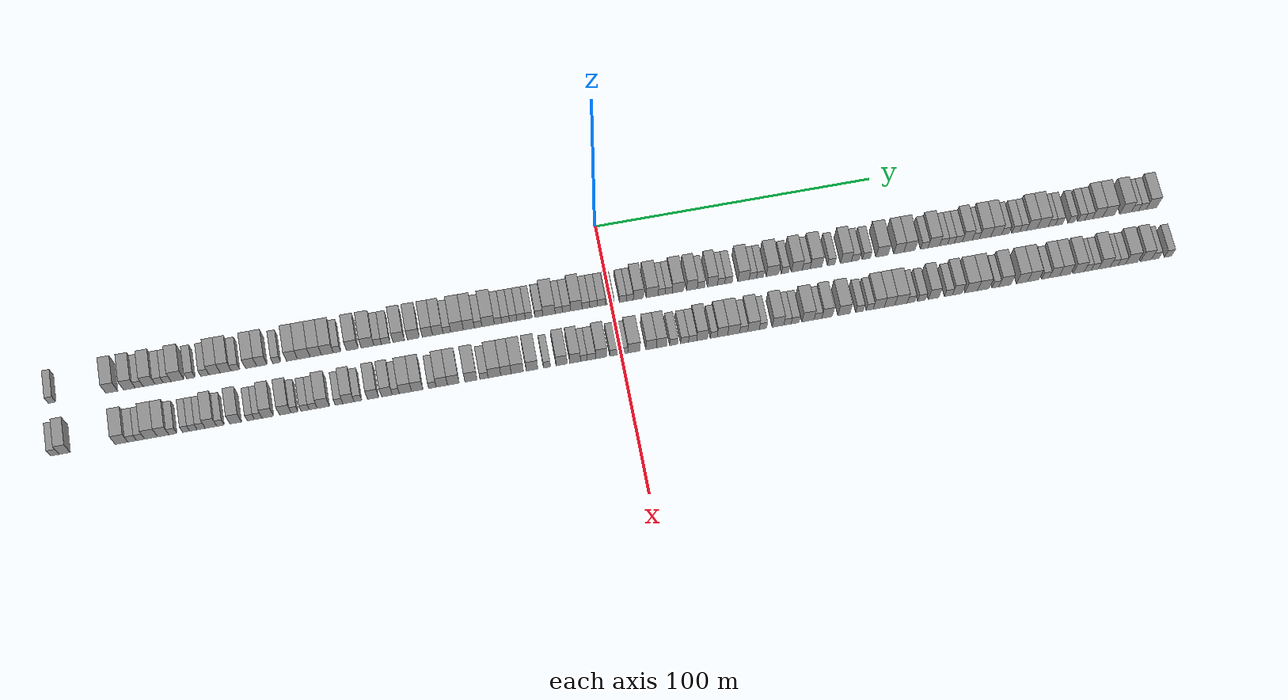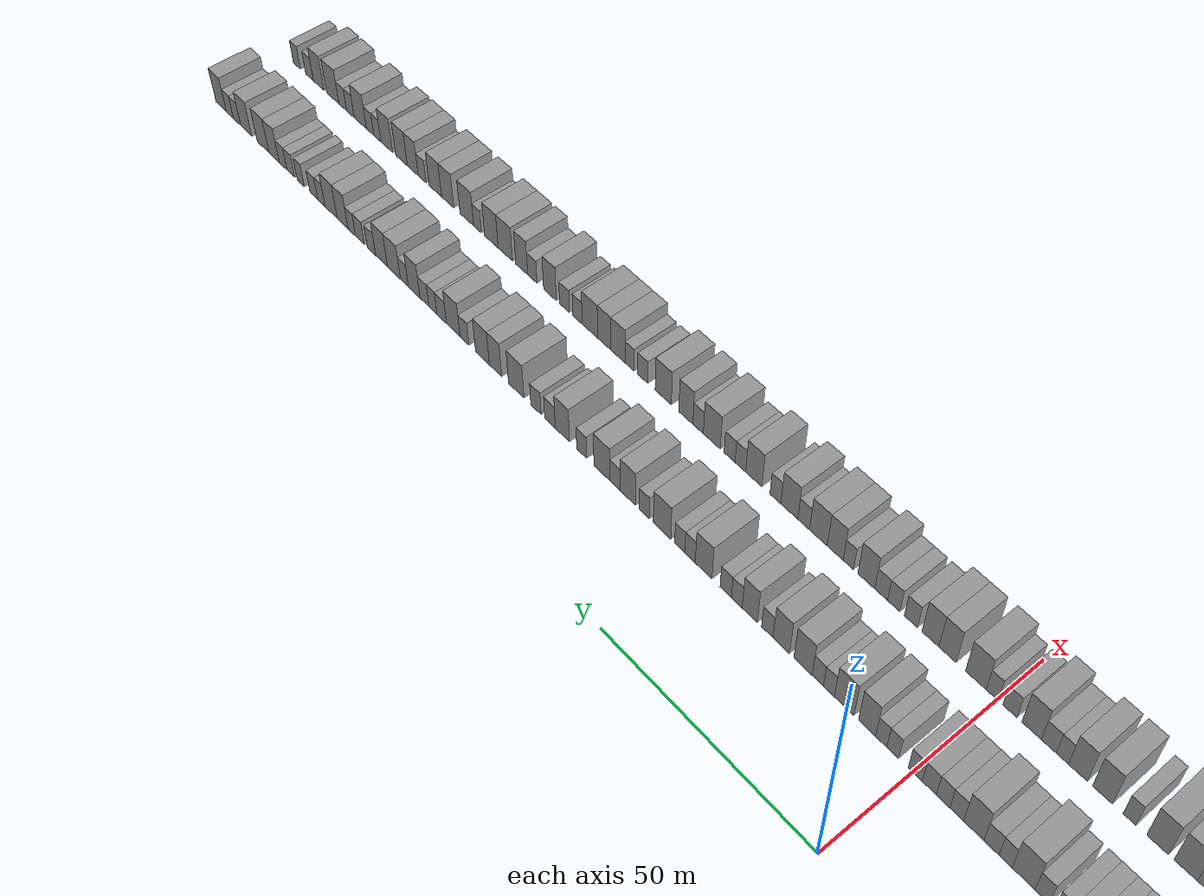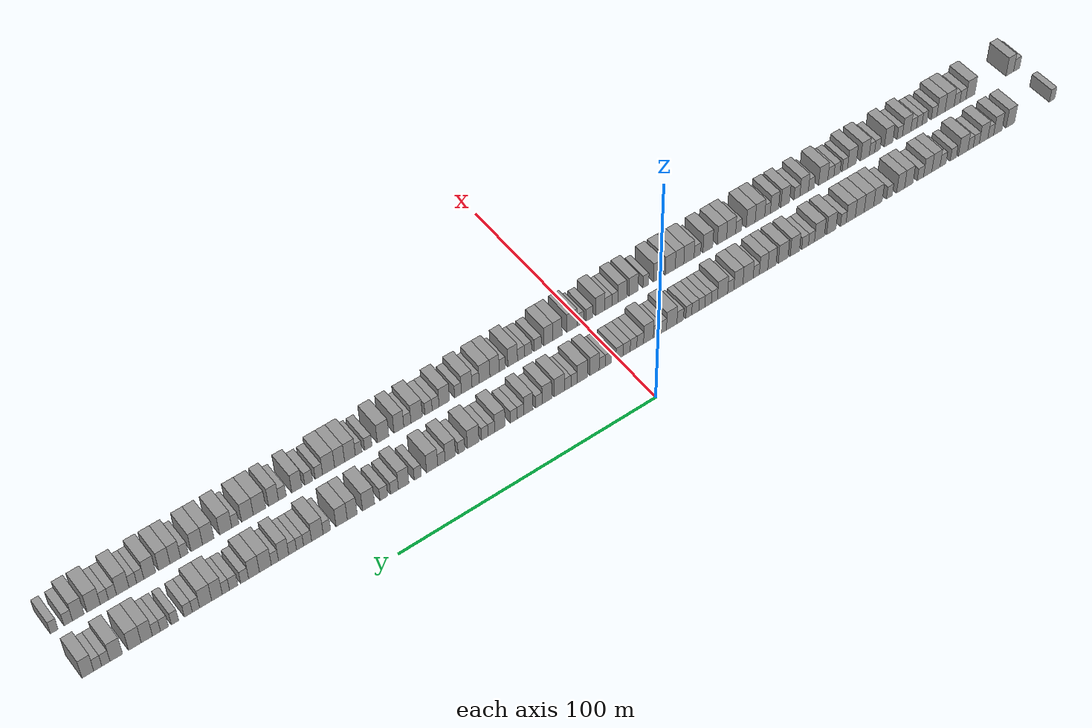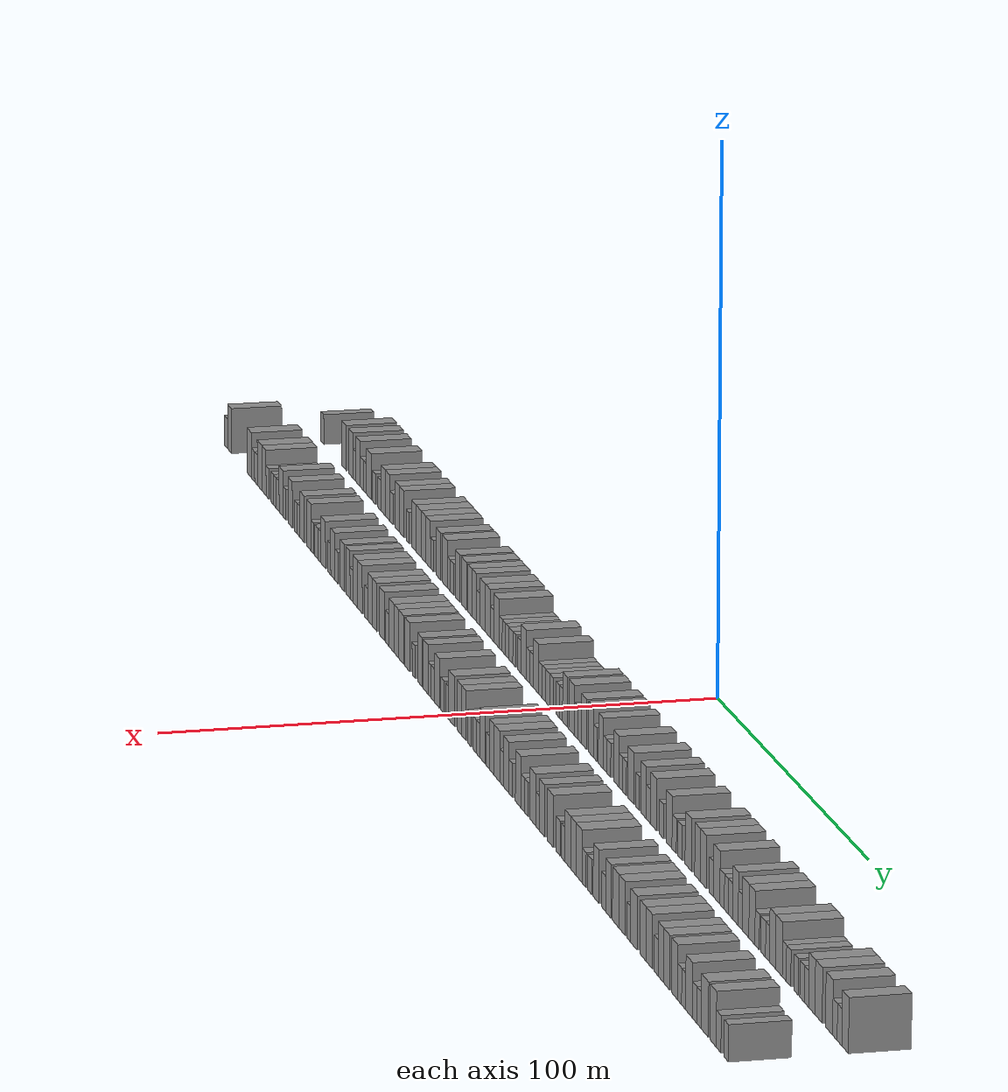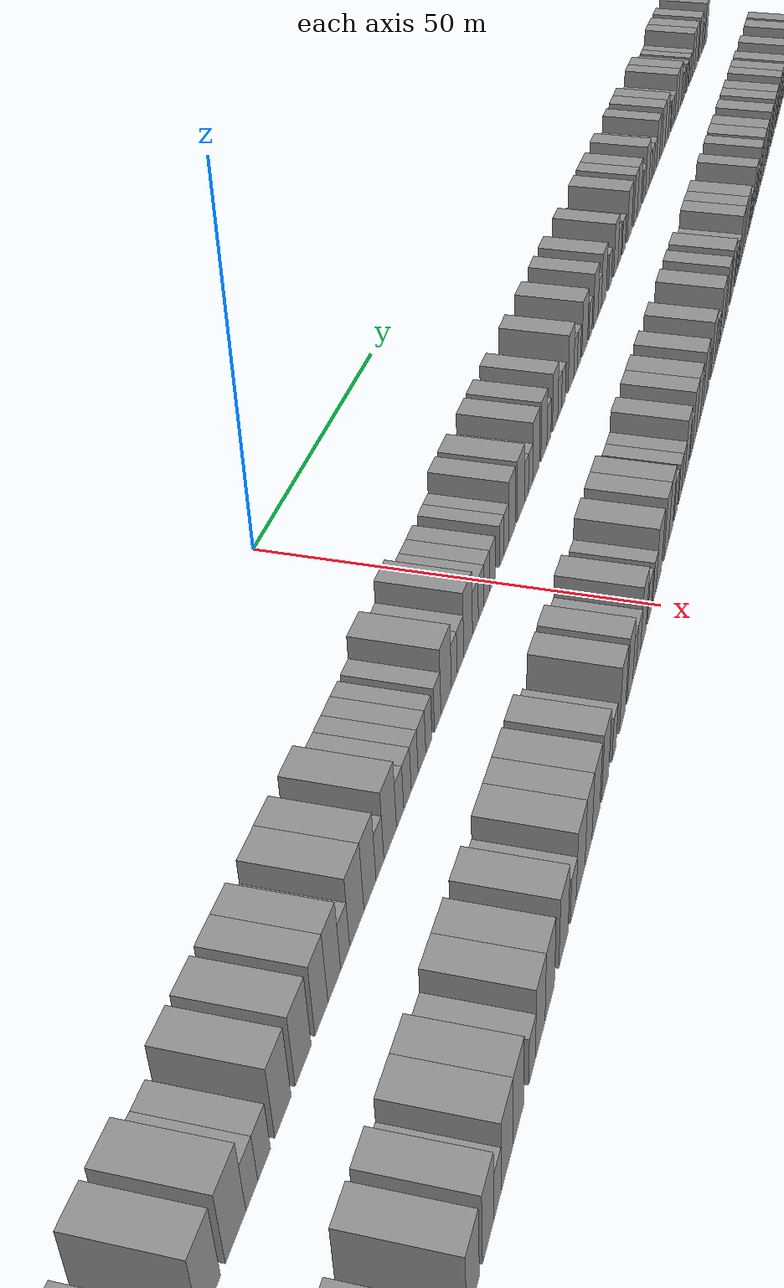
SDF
<sdf version="1.6">
 <world name="default">
  <scene>
   <sky><clouds><speed>12</speed></clouds></sky>
   <ambient>0.4 0.4 0.4 1</ambient>
   <background>0.7 0.7 0.7 1</background>
   <shadows>1</shadows>
  </scene>
  <gravity>0 0 -9.8066</gravity>
  <magnetic_field>6e-06 2.3e-05 -4.2e-05</magnetic_field>
  <physics default="0" name="default_physics" type="ode">
   <ode>
    <solver>
     <type>quick</type>
     <iters>10</iters>
     <sor>1.0</sor>
     <use_dynamic_moi_rescaling>0</use_dynamic_moi_rescaling>
    </solver>
    <constraints>
     <cfm>0</cfm>
     <erp>0.2</erp>
     <contact_max_correcting_vel>100</contact_max_correcting_vel>
     <contact_surface_layer>0.001</contact_surface_layer>
    </constraints>
   </ode>
   <max_step_size>0.004</max_step_size>
   <real_time_factor>1</real_time_factor>
   <real_time_update_rate>250</real_time_update_rate>
  </physics>
  <light name="sun" type="directional">
   <pose>0 0 10 0 0 0</pose>
   <diffuse>0.8 0.8 0.8 1</diffuse>
   <specular>0.2 0.2 0.2 1</specular>
   <attenuation>
    <range>1000</range>
    <constant>0.9</constant>
    <linear>0.01</linear>
    <quadratic>0.001</quadratic>
   </attenuation>
   <direction>-0.5 0.1 -0.9</direction>
  </light>
  <model name="building_1">
   <static>1</static>
   <pose>25.0000 -195.6918 0 0.000000 0.000000 0.000000</pose>
   <link name="link">
    <pose>0 0 3.00 0 0 0</pose>
    <collision name="collision"><geometry><box><size>10.0000 2.6163 6.0000</size></box></geometry></collision>
    <visual name="visual">
     <cast_shadows>0</cast_shadows>
     <geometry><box><size>10.0000 2.6163 6.0000</size></box></geometry>
     <material>
      <script>
       <uri>model://grey_wall/materials/scripts</uri>
       <uri>model://grey_wall/materials/textures</uri>
       <name>vrc/grey_wall</name>
      </script>
     </material>
    </visual>
   </link>
  </model>
  <model name="building_2">
   <static>1</static>
   <pose>25.0000 -175.1636 0 0.000000 0.000000 0.000000</pose>
   <link name="link">
    <pose>0 0 4.50 0 0 0</pose>
    <collision name="collision"><geometry><box><size>10.0000 4.1467 9.0000</size></box></geometry></collision>
    <visual name="visual">
     <cast_shadows>0</cast_shadows>
     <geometry><box><size>10.0000 4.1467 9.0000</size></box></geometry>
     <material>
      <script>
       <uri>model://grey_wall/materials/scripts</uri>
       <uri>model://grey_wall/materials/textures</uri>
       <name>vrc/grey_wall</name>
      </script>
     </material>
    </visual>
   </link>
  </model>
  <model name="building_3">
   <static>1</static>
   <pose>25.0000 -169.0560 0 0.000000 0.000000 0.000000</pose>
   <link name="link">
    <pose>0 0 4.50 0 0 0</pose>
    <collision name="collision"><geometry><box><size>10.0000 4.0685 9.0000</size></box></geometry></collision>
    <visual name="visual">
     <cast_shadows>0</cast_shadows>
     <geometry><box><size>10.0000 4.0685 9.0000</size></box></geometry>
     <material>
      <script>
       <uri>model://grey_wall/materials/scripts</uri>
       <uri>model://grey_wall/materials/textures</uri>
       <name>vrc/grey_wall</name>
      </script>
     </material>
    </visual>
   </link>
  </model>
  <model name="building_4">
   <static>1</static>
   <pose>25.0000 -165.6391 0 0.000000 0.000000 0.000000</pose>
   <link name="link">
    <pose>0 0 3.00 0 0 0</pose>
    <collision name="collision"><geometry><box><size>10.0000 2.7654 6.0000</size></box></geometry></collision>
    <visual name="visual">
     <cast_shadows>0</cast_shadows>
     <geometry><box><size>10.0000 2.7654 6.0000</size></box></geometry>
     <material>
      <script>
       <uri>model://grey_wall/materials/scripts</uri>
       <uri>model://grey_wall/materials/textures</uri>
       <name>vrc/grey_wall</name>
      </script>
     </material>
    </visual>
   </link>
  </model>
  <model name="building_5">
   <static>1</static>
   <pose>25.0000 -162.1850 0 0.000000 0.000000 0.000000</pose>
   <link name="link">
    <pose>0 0 4.50 0 0 0</pose>
    <collision name="collision"><geometry><box><size>10.0000 4.1427 9.0000</size></box></geometry></collision>
    <visual name="visual">
     <cast_shadows>0</cast_shadows>
     <geometry><box><size>10.0000 4.1427 9.0000</size></box></geometry>
     <material>
      <script>
       <uri>model://grey_wall/materials/scripts</uri>
       <uri>model://grey_wall/materials/textures</uri>
       <name>vrc/grey_wall</name>
      </script>
     </material>
    </visual>
   </link>
  </model>
  <model name="building_6">
   <static>1</static>
   <pose>25.0000 -158.6930 0 0.000000 0.000000 0.000000</pose>
   <link name="link">
    <pose>0 0 3.00 0 0 0</pose>
    <collision name="collision"><geometry><box><size>10.0000 2.8413 6.0000</size></box></geometry></collision>
    <visual name="visual">
     <cast_shadows>0</cast_shadows>
     <geometry><box><size>10.0000 2.8413 6.0000</size></box></geometry>
     <material>
      <script>
       <uri>model://grey_wall/materials/scripts</uri>
       <uri>model://grey_wall/materials/textures</uri>
       <name>vrc/grey_wall</name>
      </script>
     </material>
    </visual>
   </link>
  </model>
  <model name="building_7">
   <static>1</static>
   <pose>25.0000 -155.9440 0 0.000000 0.000000 0.000000</pose>
   <link name="link">
    <pose>0 0 3.00 0 0 0</pose>
    <collision name="collision"><geometry><box><size>10.0000 2.6566 6.0000</size></box></geometry></collision>
    <visual name="visual">
     <cast_shadows>0</cast_shadows>
     <geometry><box><size>10.0000 2.6566 6.0000</size></box></geometry>
     <material>
      <script>
       <uri>model://grey_wall/materials/scripts</uri>
       <uri>model://grey_wall/materials/textures</uri>
       <name>vrc/grey_wall</name>
      </script>
     </material>
    </visual>
   </link>
  </model>
  <model name="building_8">
   <static>1</static>
   <pose>25.0000 -152.3970 0 0.000000 0.000000 0.000000</pose>
   <link name="link">
    <pose>0 0 4.50 0 0 0</pose>
    <collision name="collision"><geometry><box><size>10.0000 4.4376 9.0000</size></box></geometry></collision>
    <visual name="visual">
     <cast_shadows>0</cast_shadows>
     <geometry><box><size>10.0000 4.4376 9.0000</size></box></geometry>
     <material>
      <script>
       <uri>model://grey_wall/materials/scripts</uri>
       <uri>model://grey_wall/materials/textures</uri>
       <name>vrc/grey_wall</name>
      </script>
     </material>
    </visual>
   </link>
  </model>
  <model name="building_9">
   <static>1</static>
   <pose>25.0000 -147.7334 0 0.000000 0.000000 0.000000</pose>
   <link name="link">
    <pose>0 0 3.00 0 0 0</pose>
    <collision name="collision"><geometry><box><size>10.0000 2.8895 6.0000</size></box></geometry></collision>
    <visual name="visual">
     <cast_shadows>0</cast_shadows>
     <geometry><box><size>10.0000 2.8895 6.0000</size></box></geometry>
     <material>
      <script>
       <uri>model://grey_wall/materials/scripts</uri>
       <uri>model://grey_wall/materials/textures</uri>
       <name>vrc/grey_wall</name>
      </script>
     </material>
    </visual>
   </link>
  </model>
  <model name="building_10">
   <static>1</static>
   <pose>25.0000 -142.8541 0 0.000000 0.000000 0.000000</pose>
   <link name="link">
    <pose>0 0 3.00 0 0 0</pose>
    <collision name="collision"><geometry><box><size>10.0000 2.8692 6.0000</size></box></geometry></collision>
    <visual name="visual">
     <cast_shadows>0</cast_shadows>
     <geometry><box><size>10.0000 2.8692 6.0000</size></box></geometry>
     <material>
      <script>
       <uri>model://grey_wall/materials/scripts</uri>
       <uri>model://grey_wall/materials/textures</uri>
       <name>vrc/grey_wall</name>
      </script>
     </material>
    </visual>
   </link>
  </model>
  <model name="building_11">
   <static>1</static>
   <pose>25.0000 -139.4977 0 0.000000 0.000000 0.000000</pose>
   <link name="link">
    <pose>0 0 4.50 0 0 0</pose>
    <collision name="collision"><geometry><box><size>10.0000 3.8434 9.0000</size></box></geometry></collision>
    <visual name="visual">
     <cast_shadows>0</cast_shadows>
     <geometry><box><size>10.0000 3.8434 9.0000</size></box></geometry>
     <material>
      <script>
       <uri>model://grey_wall/materials/scripts</uri>
       <uri>model://grey_wall/materials/textures</uri>
       <name>vrc/grey_wall</name>
      </script>
     </material>
    </visual>
   </link>
  </model>
  <model name="building_12">
   <static>1</static>
   <pose>25.0000 -135.6449 0 0.000000 0.000000 0.000000</pose>
   <link name="link">
    <pose>0 0 4.50 0 0 0</pose>
    <collision name="collision"><geometry><box><size>10.0000 3.8623 9.0000</size></box></geometry></collision>
    <visual name="visual">
     <cast_shadows>0</cast_shadows>
     <geometry><box><size>10.0000 3.8623 9.0000</size></box></geometry>
     <material>
      <script>
       <uri>model://grey_wall/materials/scripts</uri>
       <uri>model://grey_wall/materials/textures</uri>
       <name>vrc/grey_wall</name>
      </script>
     </material>
    </visual>
   </link>
  </model>
  <model name="building_13">
   <static>1</static>
   <pose>25.0000 -132.2493 0 0.000000 0.000000 0.000000</pose>
   <link name="link">
    <pose>0 0 3.00 0 0 0</pose>
    <collision name="collision"><geometry><box><size>10.0000 2.9291 6.0000</size></box></geometry></collision>
    <visual name="visual">
     <cast_shadows>0</cast_shadows>
     <geometry><box><size>10.0000 2.9291 6.0000</size></box></geometry>
     <material>
      <script>
       <uri>model://grey_wall/materials/scripts</uri>
       <uri>model://grey_wall/materials/textures</uri>
       <name>vrc/grey_wall</name>
      </script>
     </material>
    </visual>
   </link>
  </model>
  <model name="building_14">
   <static>1</static>
   <pose>25.0000 -126.8231 0 0.000000 0.000000 0.000000</pose>
   <link name="link">
    <pose>0 0 4.50 0 0 0</pose>
    <collision name="collision"><geometry><box><size>10.0000 3.9233 9.0000</size></box></geometry></collision>
    <visual name="visual">
     <cast_shadows>0</cast_shadows>
     <geometry><box><size>10.0000 3.9233 9.0000</size></box></geometry>
     <material>
      <script>
       <uri>model://grey_wall/materials/scripts</uri>
       <uri>model://grey_wall/materials/textures</uri>
       <name>vrc/grey_wall</name>
      </script>
     </material>
    </visual>
   </link>
  </model>
  <model name="building_15">
   <static>1</static>
   <pose>25.0000 -123.0368 0 0.000000 0.000000 0.000000</pose>
   <link name="link">
    <pose>0 0 4.50 0 0 0</pose>
    <collision name="collision"><geometry><box><size>10.0000 3.6492 9.0000</size></box></geometry></collision>
    <visual name="visual">
     <cast_shadows>0</cast_shadows>
     <geometry><box><size>10.0000 3.6492 9.0000</size></box></geometry>
     <material>
      <script>
       <uri>model://grey_wall/materials/scripts</uri>
       <uri>model://grey_wall/materials/textures</uri>
       <name>vrc/grey_wall</name>
      </script>
     </material>
    </visual>
   </link>
  </model>
  <model name="building_16">
   <static>1</static>
   <pose>25.0000 -117.8522 0 0.000000 0.000000 0.000000</pose>
   <link name="link">
    <pose>0 0 3.00 0 0 0</pose>
    <collision name="collision"><geometry><box><size>10.0000 2.7202 6.0000</size></box></geometry></collision>
    <visual name="visual">
     <cast_shadows>0</cast_shadows>
     <geometry><box><size>10.0000 2.7202 6.0000</size></box></geometry>
     <material>
      <script>
       <uri>model://grey_wall/materials/scripts</uri>
       <uri>model://grey_wall/materials/textures</uri>
       <name>vrc/grey_wall</name>
      </script>
     </material>
    </visual>
   </link>
  </model>
  <model name="building_17">
   <static>1</static>
   <pose>25.0000 -112.5469 0 0.000000 0.000000 0.000000</pose>
   <link name="link">
    <pose>0 0 4.50 0 0 0</pose>
    <collision name="collision"><geometry><box><size>10.0000 3.8903 9.0000</size></box></geometry></collision>
    <visual name="visual">
     <cast_shadows>0</cast_shadows>
     <geometry><box><size>10.0000 3.8903 9.0000</size></box></geometry>
     <material>
      <script>
       <uri>model://grey_wall/materials/scripts</uri>
       <uri>model://grey_wall/materials/textures</uri>
       <name>vrc/grey_wall</name>
      </script>
     </material>
    </visual>
   </link>
  </model>
  <model name="building_18">
   <static>1</static>
   <pose>25.0000 -108.4242 0 0.000000 0.000000 0.000000</pose>
   <link name="link">
    <pose>0 0 4.50 0 0 0</pose>
    <collision name="collision"><geometry><box><size>10.0000 4.3552 9.0000</size></box></geometry></collision>
    <visual name="visual">
     <cast_shadows>0</cast_shadows>
     <geometry><box><size>10.0000 4.3552 9.0000</size></box></geometry>
     <material>
      <script>
       <uri>model://grey_wall/materials/scripts</uri>
       <uri>model://grey_wall/materials/textures</uri>
       <name>vrc/grey_wall</name>
      </script>
     </material>
    </visual>
   </link>
  </model>
  <model name="building_19">
   <static>1</static>
   <pose>25.0000 -104.2373 0 0.000000 0.000000 0.000000</pose>
   <link name="link">
    <pose>0 0 4.50 0 0 0</pose>
    <collision name="collision"><geometry><box><size>10.0000 4.0187 9.0000</size></box></geometry></collision>
    <visual name="visual">
     <cast_shadows>0</cast_shadows>
     <geometry><box><size>10.0000 4.0187 9.0000</size></box></geometry>
     <material>
      <script>
       <uri>model://grey_wall/materials/scripts</uri>
       <uri>model://grey_wall/materials/textures</uri>
       <name>vrc/grey_wall</name>
      </script>
     </material>
    </visual>
   </link>
  </model>
  <model name="building_20">
   <static>1</static>
   <pose>25.0000 -100.1476 0 0.000000 0.000000 0.000000</pose>
   <link name="link">
    <pose>0 0 4.50 0 0 0</pose>
    <collision name="collision"><geometry><box><size>10.0000 4.1608 9.0000</size></box></geometry></collision>
    <visual name="visual">
     <cast_shadows>0</cast_shadows>
     <geometry><box><size>10.0000 4.1608 9.0000</size></box></geometry>
     <material>
      <script>
       <uri>model://grey_wall/materials/scripts</uri>
       <uri>model://grey_wall/materials/textures</uri>
       <name>vrc/grey_wall</name>
      </script>
     </material>
    </visual>
   </link>
  </model>
  <model name="building_21">
   <static>1</static>
   <pose>25.0000 -96.7833 0 0.000000 0.000000 0.000000</pose>
   <link name="link">
    <pose>0 0 3.00 0 0 0</pose>
    <collision name="collision"><geometry><box><size>10.0000 2.5677 6.0000</size></box></geometry></collision>
    <visual name="visual">
     <cast_shadows>0</cast_shadows>
     <geometry><box><size>10.0000 2.5677 6.0000</size></box></geometry>
     <material>
      <script>
       <uri>model://grey_wall/materials/scripts</uri>
       <uri>model://grey_wall/materials/textures</uri>
       <name>vrc/grey_wall</name>
      </script>
     </material>
    </visual>
   </link>
  </model>
  <model name="building_22">
   <static>1</static>
   <pose>25.0000 -91.4115 0 0.000000 0.000000 0.000000</pose>
   <link name="link">
    <pose>0 0 4.50 0 0 0</pose>
    <collision name="collision"><geometry><box><size>10.0000 4.1758 9.0000</size></box></geometry></collision>
    <visual name="visual">
     <cast_shadows>0</cast_shadows>
     <geometry><box><size>10.0000 4.1758 9.0000</size></box></geometry>
     <material>
      <script>
       <uri>model://grey_wall/materials/scripts</uri>
       <uri>model://grey_wall/materials/textures</uri>
       <name>vrc/grey_wall</name>
      </script>
     </material>
    </visual>
   </link>
  </model>
  <model name="building_23">
   <static>1</static>
   <pose>25.0000 -86.0870 0 0.000000 0.000000 0.000000</pose>
   <link name="link">
    <pose>0 0 4.50 0 0 0</pose>
    <collision name="collision"><geometry><box><size>10.0000 4.4732 9.0000</size></box></geometry></collision>
    <visual name="visual">
     <cast_shadows>0</cast_shadows>
     <geometry><box><size>10.0000 4.4732 9.0000</size></box></geometry>
     <material>
      <script>
       <uri>model://grey_wall/materials/scripts</uri>
       <uri>model://grey_wall/materials/textures</uri>
       <name>vrc/grey_wall</name>
      </script>
     </material>
    </visual>
   </link>
  </model>
  <model name="building_24">
   <static>1</static>
   <pose>25.0000 -82.5072 0 0.000000 0.000000 0.000000</pose>
   <link name="link">
    <pose>0 0 3.00 0 0 0</pose>
    <collision name="collision"><geometry><box><size>10.0000 2.6864 6.0000</size></box></geometry></collision>
    <visual name="visual">
     <cast_shadows>0</cast_shadows>
     <geometry><box><size>10.0000 2.6864 6.0000</size></box></geometry>
     <material>
      <script>
       <uri>model://grey_wall/materials/scripts</uri>
       <uri>model://grey_wall/materials/textures</uri>
       <name>vrc/grey_wall</name>
      </script>
     </material>
    </visual>
   </link>
  </model>
  <model name="building_25">
   <static>1</static>
   <pose>25.0000 -79.6708 0 0.000000 0.000000 0.000000</pose>
   <link name="link">
    <pose>0 0 3.00 0 0 0</pose>
    <collision name="collision"><geometry><box><size>10.0000 2.9863 6.0000</size></box></geometry></collision>
    <visual name="visual">
     <cast_shadows>0</cast_shadows>
     <geometry><box><size>10.0000 2.9863 6.0000</size></box></geometry>
     <material>
      <script>
       <uri>model://grey_wall/materials/scripts</uri>
       <uri>model://grey_wall/materials/textures</uri>
       <name>vrc/grey_wall</name>
      </script>
     </material>
    </visual>
   </link>
  </model>
  <model name="building_26">
   <static>1</static>
   <pose>25.0000 -75.1414 0 0.000000 0.000000 0.000000</pose>
   <link name="link">
    <pose>0 0 4.50 0 0 0</pose>
    <collision name="collision"><geometry><box><size>10.0000 4.0725 9.0000</size></box></geometry></collision>
    <visual name="visual">
     <cast_shadows>0</cast_shadows>
     <geometry><box><size>10.0000 4.0725 9.0000</size></box></geometry>
     <material>
      <script>
       <uri>model://grey_wall/materials/scripts</uri>
       <uri>model://grey_wall/materials/textures</uri>
       <name>vrc/grey_wall</name>
      </script>
     </material>
    </visual>
   </link>
  </model>
  <model name="building_27">
   <static>1</static>
   <pose>25.0000 -69.9814 0 0.000000 0.000000 0.000000</pose>
   <link name="link">
    <pose>0 0 4.50 0 0 0</pose>
    <collision name="collision"><geometry><box><size>10.0000 4.2475 9.0000</size></box></geometry></collision>
    <visual name="visual">
     <cast_shadows>0</cast_shadows>
     <geometry><box><size>10.0000 4.2475 9.0000</size></box></geometry>
     <material>
      <script>
       <uri>model://grey_wall/materials/scripts</uri>
       <uri>model://grey_wall/materials/textures</uri>
       <name>vrc/grey_wall</name>
      </script>
     </material>
    </visual>
   </link>
  </model>
  <model name="building_28">
   <static>1</static>
   <pose>25.0000 -65.0414 0 0.000000 0.000000 0.000000</pose>
   <link name="link">
    <pose>0 0 4.50 0 0 0</pose>
    <collision name="collision"><geometry><box><size>10.0000 3.6324 9.0000</size></box></geometry></collision>
    <visual name="visual">
     <cast_shadows>0</cast_shadows>
     <geometry><box><size>10.0000 3.6324 9.0000</size></box></geometry>
     <material>
      <script>
       <uri>model://grey_wall/materials/scripts</uri>
       <uri>model://grey_wall/materials/textures</uri>
       <name>vrc/grey_wall</name>
      </script>
     </material>
    </visual>
   </link>
  </model>
  <model name="building_29">
   <static>1</static>
   <pose>25.0000 -61.3847 0 0.000000 0.000000 0.000000</pose>
   <link name="link">
    <pose>0 0 4.50 0 0 0</pose>
    <collision name="collision"><geometry><box><size>10.0000 3.6810 9.0000</size></box></geometry></collision>
    <visual name="visual">
     <cast_shadows>0</cast_shadows>
     <geometry><box><size>10.0000 3.6810 9.0000</size></box></geometry>
     <material>
      <script>
       <uri>model://grey_wall/materials/scripts</uri>
       <uri>model://grey_wall/materials/textures</uri>
       <name>vrc/grey_wall</name>
      </script>
     </material>
    </visual>
   </link>
  </model>
  <model name="building_30">
   <static>1</static>
   <pose>25.0000 -58.1936 0 0.000000 0.000000 0.000000</pose>
   <link name="link">
    <pose>0 0 3.00 0 0 0</pose>
    <collision name="collision"><geometry><box><size>10.0000 2.7013 6.0000</size></box></geometry></collision>
    <visual name="visual">
     <cast_shadows>0</cast_shadows>
     <geometry><box><size>10.0000 2.7013 6.0000</size></box></geometry>
     <material>
      <script>
       <uri>model://grey_wall/materials/scripts</uri>
       <uri>model://grey_wall/materials/textures</uri>
       <name>vrc/grey_wall</name>
      </script>
     </material>
    </visual>
   </link>
  </model>
  <model name="building_31">
   <static>1</static>
   <pose>25.0000 -54.6182 0 0.000000 0.000000 0.000000</pose>
   <link name="link">
    <pose>0 0 4.50 0 0 0</pose>
    <collision name="collision"><geometry><box><size>10.0000 4.4496 9.0000</size></box></geometry></collision>
    <visual name="visual">
     <cast_shadows>0</cast_shadows>
     <geometry><box><size>10.0000 4.4496 9.0000</size></box></geometry>
     <material>
      <script>
       <uri>model://grey_wall/materials/scripts</uri>
       <uri>model://grey_wall/materials/textures</uri>
       <name>vrc/grey_wall</name>
      </script>
     </material>
    </visual>
   </link>
  </model>
  <model name="building_32">
   <static>1</static>
   <pose>25.0000 -50.4423 0 0.000000 0.000000 0.000000</pose>
   <link name="link">
    <pose>0 0 4.50 0 0 0</pose>
    <collision name="collision"><geometry><box><size>10.0000 3.9020 9.0000</size></box></geometry></collision>
    <visual name="visual">
     <cast_shadows>0</cast_shadows>
     <geometry><box><size>10.0000 3.9020 9.0000</size></box></geometry>
     <material>
      <script>
       <uri>model://grey_wall/materials/scripts</uri>
       <uri>model://grey_wall/materials/textures</uri>
       <name>vrc/grey_wall</name>
      </script>
     </material>
    </visual>
   </link>
  </model>
  <model name="building_33">
   <static>1</static>
   <pose>25.0000 -47.1648 0 0.000000 0.000000 0.000000</pose>
   <link name="link">
    <pose>0 0 3.00 0 0 0</pose>
    <collision name="collision"><geometry><box><size>10.0000 2.6529 6.0000</size></box></geometry></collision>
    <visual name="visual">
     <cast_shadows>0</cast_shadows>
     <geometry><box><size>10.0000 2.6529 6.0000</size></box></geometry>
     <material>
      <script>
       <uri>model://grey_wall/materials/scripts</uri>
       <uri>model://grey_wall/materials/textures</uri>
       <name>vrc/grey_wall</name>
      </script>
     </material>
    </visual>
   </link>
  </model>
  <model name="building_34">
   <static>1</static>
   <pose>25.0000 -43.6502 0 0.000000 0.000000 0.000000</pose>
   <link name="link">
    <pose>0 0 4.50 0 0 0</pose>
    <collision name="collision"><geometry><box><size>10.0000 4.3764 9.0000</size></box></geometry></collision>
    <visual name="visual">
     <cast_shadows>0</cast_shadows>
     <geometry><box><size>10.0000 4.3764 9.0000</size></box></geometry>
     <material>
      <script>
       <uri>model://grey_wall/materials/scripts</uri>
       <uri>model://grey_wall/materials/textures</uri>
       <name>vrc/grey_wall</name>
      </script>
     </material>
    </visual>
   </link>
  </model>
  <model name="building_35">
   <static>1</static>
   <pose>25.0000 -40.1557 0 0.000000 0.000000 0.000000</pose>
   <link name="link">
    <pose>0 0 3.00 0 0 0</pose>
    <collision name="collision"><geometry><box><size>10.0000 2.6125 6.0000</size></box></geometry></collision>
    <visual name="visual">
     <cast_shadows>0</cast_shadows>
     <geometry><box><size>10.0000 2.6125 6.0000</size></box></geometry>
     <material>
      <script>
       <uri>model://grey_wall/materials/scripts</uri>
       <uri>model://grey_wall/materials/textures</uri>
       <name>vrc/grey_wall</name>
      </script>
     </material>
    </visual>
   </link>
  </model>
  <model name="building_36">
   <static>1</static>
   <pose>25.0000 -37.4683 0 0.000000 0.000000 0.000000</pose>
   <link name="link">
    <pose>0 0 3.00 0 0 0</pose>
    <collision name="collision"><geometry><box><size>10.0000 2.7624 6.0000</size></box></geometry></collision>
    <visual name="visual">
     <cast_shadows>0</cast_shadows>
     <geometry><box><size>10.0000 2.7624 6.0000</size></box></geometry>
     <material>
      <script>
       <uri>model://grey_wall/materials/scripts</uri>
       <uri>model://grey_wall/materials/textures</uri>
       <name>vrc/grey_wall</name>
      </script>
     </material>
    </visual>
   </link>
  </model>
  <model name="building_37">
   <static>1</static>
   <pose>25.0000 -34.7901 0 0.000000 0.000000 0.000000</pose>
   <link name="link">
    <pose>0 0 3.00 0 0 0</pose>
    <collision name="collision"><geometry><box><size>10.0000 2.5939 6.0000</size></box></geometry></collision>
    <visual name="visual">
     <cast_shadows>0</cast_shadows>
     <geometry><box><size>10.0000 2.5939 6.0000</size></box></geometry>
     <material>
      <script>
       <uri>model://grey_wall/materials/scripts</uri>
       <uri>model://grey_wall/materials/textures</uri>
       <name>vrc/grey_wall</name>
      </script>
     </material>
    </visual>
   </link>
  </model>
  <model name="building_38">
   <static>1</static>
   <pose>25.0000 -31.9998 0 0.000000 0.000000 0.000000</pose>
   <link name="link">
    <pose>0 0 3.00 0 0 0</pose>
    <collision name="collision"><geometry><box><size>10.0000 2.9867 6.0000</size></box></geometry></collision>
    <visual name="visual">
     <cast_shadows>0</cast_shadows>
     <geometry><box><size>10.0000 2.9867 6.0000</size></box></geometry>
     <material>
      <script>
       <uri>model://grey_wall/materials/scripts</uri>
       <uri>model://grey_wall/materials/textures</uri>
       <name>vrc/grey_wall</name>
      </script>
     </material>
    </visual>
   </link>
  </model>
  <model name="building_39">
   <static>1</static>
   <pose>25.0000 -29.2741 0 0.000000 0.000000 0.000000</pose>
   <link name="link">
    <pose>0 0 3.00 0 0 0</pose>
    <collision name="collision"><geometry><box><size>10.0000 2.4649 6.0000</size></box></geometry></collision>
    <visual name="visual">
     <cast_shadows>0</cast_shadows>
     <geometry><box><size>10.0000 2.4649 6.0000</size></box></geometry>
     <material>
      <script>
       <uri>model://grey_wall/materials/scripts</uri>
       <uri>model://grey_wall/materials/textures</uri>
       <name>vrc/grey_wall</name>
      </script>
     </material>
    </visual>
   </link>
  </model>
  <model name="building_40">
   <static>1</static>
   <pose>25.0000 -25.6696 0 0.000000 0.000000 0.000000</pose>
   <link name="link">
    <pose>0 0 3.00 0 0 0</pose>
    <collision name="collision"><geometry><box><size>10.0000 2.7440 6.0000</size></box></geometry></collision>
    <visual name="visual">
     <cast_shadows>0</cast_shadows>
     <geometry><box><size>10.0000 2.7440 6.0000</size></box></geometry>
     <material>
      <script>
       <uri>model://grey_wall/materials/scripts</uri>
       <uri>model://grey_wall/materials/textures</uri>
       <name>vrc/grey_wall</name>
      </script>
     </material>
    </visual>
   </link>
  </model>
  <model name="building_41">
   <static>1</static>
   <pose>25.0000 -22.1015 0 0.000000 0.000000 0.000000</pose>
   <link name="link">
    <pose>0 0 4.50 0 0 0</pose>
    <collision name="collision"><geometry><box><size>10.0000 4.3921 9.0000</size></box></geometry></collision>
    <visual name="visual">
     <cast_shadows>0</cast_shadows>
     <geometry><box><size>10.0000 4.3921 9.0000</size></box></geometry>
     <material>
      <script>
       <uri>model://grey_wall/materials/scripts</uri>
       <uri>model://grey_wall/materials/textures</uri>
       <name>vrc/grey_wall</name>
      </script>
     </material>
    </visual>
   </link>
  </model>
  <model name="building_42">
   <static>1</static>
   <pose>25.0000 -18.6180 0 0.000000 0.000000 0.000000</pose>
   <link name="link">
    <pose>0 0 3.00 0 0 0</pose>
    <collision name="collision"><geometry><box><size>10.0000 2.5749 6.0000</size></box></geometry></collision>
    <visual name="visual">
     <cast_shadows>0</cast_shadows>
     <geometry><box><size>10.0000 2.5749 6.0000</size></box></geometry>
     <material>
      <script>
       <uri>model://grey_wall/materials/scripts</uri>
       <uri>model://grey_wall/materials/textures</uri>
       <name>vrc/grey_wall</name>
      </script>
     </material>
    </visual>
   </link>
  </model>
  <model name="building_43">
   <static>1</static>
   <pose>25.0000 -15.8594 0 0.000000 0.000000 0.000000</pose>
   <link name="link">
    <pose>0 0 3.00 0 0 0</pose>
    <collision name="collision"><geometry><box><size>10.0000 2.9423 6.0000</size></box></geometry></collision>
    <visual name="visual">
     <cast_shadows>0</cast_shadows>
     <geometry><box><size>10.0000 2.9423 6.0000</size></box></geometry>
     <material>
      <script>
       <uri>model://grey_wall/materials/scripts</uri>
       <uri>model://grey_wall/materials/textures</uri>
       <name>vrc/grey_wall</name>
      </script>
     </material>
    </visual>
   </link>
  </model>
  <model name="building_44">
   <static>1</static>
   <pose>25.0000 -12.3718 0 0.000000 0.000000 0.000000</pose>
   <link name="link">
    <pose>0 0 4.50 0 0 0</pose>
    <collision name="collision"><geometry><box><size>10.0000 4.0329 9.0000</size></box></geometry></collision>
    <visual name="visual">
     <cast_shadows>0</cast_shadows>
     <geometry><box><size>10.0000 4.0329 9.0000</size></box></geometry>
     <material>
      <script>
       <uri>model://grey_wall/materials/scripts</uri>
       <uri>model://grey_wall/materials/textures</uri>
       <name>vrc/grey_wall</name>
      </script>
     </material>
    </visual>
   </link>
  </model>
  <model name="building_45">
   <static>1</static>
   <pose>25.0000 -8.9670 0 0.000000 0.000000 0.000000</pose>
   <link name="link">
    <pose>0 0 3.00 0 0 0</pose>
    <collision name="collision"><geometry><box><size>10.0000 2.7767 6.0000</size></box></geometry></collision>
    <visual name="visual">
     <cast_shadows>0</cast_shadows>
     <geometry><box><size>10.0000 2.7767 6.0000</size></box></geometry>
     <material>
      <script>
       <uri>model://grey_wall/materials/scripts</uri>
       <uri>model://grey_wall/materials/textures</uri>
       <name>vrc/grey_wall</name>
      </script>
     </material>
    </visual>
   </link>
  </model>
  <model name="building_46">
   <static>1</static>
   <pose>25.0000 -6.2031 0 0.000000 0.000000 0.000000</pose>
   <link name="link">
    <pose>0 0 3.00 0 0 0</pose>
    <collision name="collision"><geometry><box><size>10.0000 2.7511 6.0000</size></box></geometry></collision>
    <visual name="visual">
     <cast_shadows>0</cast_shadows>
     <geometry><box><size>10.0000 2.7511 6.0000</size></box></geometry>
     <material>
      <script>
       <uri>model://grey_wall/materials/scripts</uri>
       <uri>model://grey_wall/materials/textures</uri>
       <name>vrc/grey_wall</name>
      </script>
     </material>
    </visual>
   </link>
  </model>
  <model name="building_47">
   <static>1</static>
   <pose>25.0000 -3.3854 0 0.000000 0.000000 0.000000</pose>
   <link name="link">
    <pose>0 0 3.00 0 0 0</pose>
    <collision name="collision"><geometry><box><size>10.0000 2.8842 6.0000</size></box></geometry></collision>
    <visual name="visual">
     <cast_shadows>0</cast_shadows>
     <geometry><box><size>10.0000 2.8842 6.0000</size></box></geometry>
     <material>
      <script>
       <uri>model://grey_wall/materials/scripts</uri>
       <uri>model://grey_wall/materials/textures</uri>
       <name>vrc/grey_wall</name>
      </script>
     </material>
    </visual>
   </link>
  </model>
  <model name="building_48">
   <static>1</static>
   <pose>25.0000 -0.4800 0 0.000000 0.000000 0.000000</pose>
   <link name="link">
    <pose>0 0 3.00 0 0 0</pose>
    <collision name="collision"><geometry><box><size>10.0000 2.9267 6.0000</size></box></geometry></collision>
    <visual name="visual">
     <cast_shadows>0</cast_shadows>
     <geometry><box><size>10.0000 2.9267 6.0000</size></box></geometry>
     <material>
      <script>
       <uri>model://grey_wall/materials/scripts</uri>
       <uri>model://grey_wall/materials/textures</uri>
       <name>vrc/grey_wall</name>
      </script>
     </material>
    </visual>
   </link>
  </model>
  <model name="building_49">
   <static>1</static>
   <pose>25.0000 4.2375 0 0.000000 0.000000 0.000000</pose>
   <link name="link">
    <pose>0 0 3.00 0 0 0</pose>
    <collision name="collision"><geometry><box><size>10.0000 2.5082 6.0000</size></box></geometry></collision>
    <visual name="visual">
     <cast_shadows>0</cast_shadows>
     <geometry><box><size>10.0000 2.5082 6.0000</size></box></geometry>
     <material>
      <script>
       <uri>model://grey_wall/materials/scripts</uri>
       <uri>model://grey_wall/materials/textures</uri>
       <name>vrc/grey_wall</name>
      </script>
     </material>
    </visual>
   </link>
  </model>
  <model name="building_50">
   <static>1</static>
   <pose>25.0000 6.7086 0 0.000000 0.000000 0.000000</pose>
   <link name="link">
    <pose>0 0 3.00 0 0 0</pose>
    <collision name="collision"><geometry><box><size>10.0000 2.4341 6.0000</size></box></geometry></collision>
    <visual name="visual">
     <cast_shadows>0</cast_shadows>
     <geometry><box><size>10.0000 2.4341 6.0000</size></box></geometry>
     <material>
      <script>
       <uri>model://grey_wall/materials/scripts</uri>
       <uri>model://grey_wall/materials/textures</uri>
       <name>vrc/grey_wall</name>
      </script>
     </material>
    </visual>
   </link>
  </model>
  <model name="building_51">
   <static>1</static>
   <pose>25.0000 9.7487 0 0.000000 0.000000 0.000000</pose>
   <link name="link">
    <pose>0 0 4.50 0 0 0</pose>
    <collision name="collision"><geometry><box><size>10.0000 3.6459 9.0000</size></box></geometry></collision>
    <visual name="visual">
     <cast_shadows>0</cast_shadows>
     <geometry><box><size>10.0000 3.6459 9.0000</size></box></geometry>
     <material>
      <script>
       <uri>model://grey_wall/materials/scripts</uri>
       <uri>model://grey_wall/materials/textures</uri>
       <name>vrc/grey_wall</name>
      </script>
     </material>
    </visual>
   </link>
  </model>
  <model name="building_52">
   <static>1</static>
   <pose>25.0000 14.7281 0 0.000000 0.000000 0.000000</pose>
   <link name="link">
    <pose>0 0 4.50 0 0 0</pose>
    <collision name="collision"><geometry><box><size>10.0000 4.3130 9.0000</size></box></geometry></collision>
    <visual name="visual">
     <cast_shadows>0</cast_shadows>
     <geometry><box><size>10.0000 4.3130 9.0000</size></box></geometry>
     <material>
      <script>
       <uri>model://grey_wall/materials/scripts</uri>
       <uri>model://grey_wall/materials/textures</uri>
       <name>vrc/grey_wall</name>
      </script>
     </material>
    </visual>
   </link>
  </model>
  <model name="building_53">
   <static>1</static>
   <pose>25.0000 18.1000 0 0.000000 0.000000 0.000000</pose>
   <link name="link">
    <pose>0 0 3.00 0 0 0</pose>
    <collision name="collision"><geometry><box><size>10.0000 2.4307 6.0000</size></box></geometry></collision>
    <visual name="visual">
     <cast_shadows>0</cast_shadows>
     <geometry><box><size>10.0000 2.4307 6.0000</size></box></geometry>
     <material>
      <script>
       <uri>model://grey_wall/materials/scripts</uri>
       <uri>model://grey_wall/materials/textures</uri>
       <name>vrc/grey_wall</name>
      </script>
     </material>
    </visual>
   </link>
  </model>
  <model name="building_54">
   <static>1</static>
   <pose>25.0000 20.5877 0 0.000000 0.000000 0.000000</pose>
   <link name="link">
    <pose>0 0 3.00 0 0 0</pose>
    <collision name="collision"><geometry><box><size>10.0000 2.5447 6.0000</size></box></geometry></collision>
    <visual name="visual">
     <cast_shadows>0</cast_shadows>
     <geometry><box><size>10.0000 2.5447 6.0000</size></box></geometry>
     <material>
      <script>
       <uri>model://grey_wall/materials/scripts</uri>
       <uri>model://grey_wall/materials/textures</uri>
       <name>vrc/grey_wall</name>
      </script>
     </material>
    </visual>
   </link>
  </model>
  <model name="building_55">
   <static>1</static>
   <pose>25.0000 23.9229 0 0.000000 0.000000 0.000000</pose>
   <link name="link">
    <pose>0 0 4.50 0 0 0</pose>
    <collision name="collision"><geometry><box><size>10.0000 4.1257 9.0000</size></box></geometry></collision>
    <visual name="visual">
     <cast_shadows>0</cast_shadows>
     <geometry><box><size>10.0000 4.1257 9.0000</size></box></geometry>
     <material>
      <script>
       <uri>model://grey_wall/materials/scripts</uri>
       <uri>model://grey_wall/materials/textures</uri>
       <name>vrc/grey_wall</name>
      </script>
     </material>
    </visual>
   </link>
  </model>
  <model name="building_56">
   <static>1</static>
   <pose>25.0000 28.8946 0 0.000000 0.000000 0.000000</pose>
   <link name="link">
    <pose>0 0 4.50 0 0 0</pose>
    <collision name="collision"><geometry><box><size>10.0000 3.8179 9.0000</size></box></geometry></collision>
    <visual name="visual">
     <cast_shadows>0</cast_shadows>
     <geometry><box><size>10.0000 3.8179 9.0000</size></box></geometry>
     <material>
      <script>
       <uri>model://grey_wall/materials/scripts</uri>
       <uri>model://grey_wall/materials/textures</uri>
       <name>vrc/grey_wall</name>
      </script>
     </material>
    </visual>
   </link>
  </model>
  <model name="building_57">
   <static>1</static>
   <pose>25.0000 32.1456 0 0.000000 0.000000 0.000000</pose>
   <link name="link">
    <pose>0 0 3.00 0 0 0</pose>
    <collision name="collision"><geometry><box><size>10.0000 2.6839 6.0000</size></box></geometry></collision>
    <visual name="visual">
     <cast_shadows>0</cast_shadows>
     <geometry><box><size>10.0000 2.6839 6.0000</size></box></geometry>
     <material>
      <script>
       <uri>model://grey_wall/materials/scripts</uri>
       <uri>model://grey_wall/materials/textures</uri>
       <name>vrc/grey_wall</name>
      </script>
     </material>
    </visual>
   </link>
  </model>
  <model name="building_58">
   <static>1</static>
   <pose>25.0000 36.2877 0 0.000000 0.000000 0.000000</pose>
   <link name="link">
    <pose>0 0 4.50 0 0 0</pose>
    <collision name="collision"><geometry><box><size>10.0000 3.6005 9.0000</size></box></geometry></collision>
    <visual name="visual">
     <cast_shadows>0</cast_shadows>
     <geometry><box><size>10.0000 3.6005 9.0000</size></box></geometry>
     <material>
      <script>
       <uri>model://grey_wall/materials/scripts</uri>
       <uri>model://grey_wall/materials/textures</uri>
       <name>vrc/grey_wall</name>
      </script>
     </material>
    </visual>
   </link>
  </model>
  <model name="building_59">
   <static>1</static>
   <pose>25.0000 39.3707 0 0.000000 0.000000 0.000000</pose>
   <link name="link">
    <pose>0 0 3.00 0 0 0</pose>
    <collision name="collision"><geometry><box><size>10.0000 2.5655 6.0000</size></box></geometry></collision>
    <visual name="visual">
     <cast_shadows>0</cast_shadows>
     <geometry><box><size>10.0000 2.5655 6.0000</size></box></geometry>
     <material>
      <script>
       <uri>model://grey_wall/materials/scripts</uri>
       <uri>model://grey_wall/materials/textures</uri>
       <name>vrc/grey_wall</name>
      </script>
     </material>
    </visual>
   </link>
  </model>
  <model name="building_60">
   <static>1</static>
   <pose>25.0000 42.0152 0 0.000000 0.000000 0.000000</pose>
   <link name="link">
    <pose>0 0 3.00 0 0 0</pose>
    <collision name="collision"><geometry><box><size>10.0000 2.7235 6.0000</size></box></geometry></collision>
    <visual name="visual">
     <cast_shadows>0</cast_shadows>
     <geometry><box><size>10.0000 2.7235 6.0000</size></box></geometry>
     <material>
      <script>
       <uri>model://grey_wall/materials/scripts</uri>
       <uri>model://grey_wall/materials/textures</uri>
       <name>vrc/grey_wall</name>
      </script>
     </material>
    </visual>
   </link>
  </model>
  <model name="building_61">
   <static>1</static>
   <pose>25.0000 47.4285 0 0.000000 0.000000 0.000000</pose>
   <link name="link">
    <pose>0 0 4.50 0 0 0</pose>
    <collision name="collision"><geometry><box><size>10.0000 4.1031 9.0000</size></box></geometry></collision>
    <visual name="visual">
     <cast_shadows>0</cast_shadows>
     <geometry><box><size>10.0000 4.1031 9.0000</size></box></geometry>
     <material>
      <script>
       <uri>model://grey_wall/materials/scripts</uri>
       <uri>model://grey_wall/materials/textures</uri>
       <name>vrc/grey_wall</name>
      </script>
     </material>
    </visual>
   </link>
  </model>
  <model name="building_62">
   <static>1</static>
   <pose>25.0000 50.7780 0 0.000000 0.000000 0.000000</pose>
   <link name="link">
    <pose>0 0 3.00 0 0 0</pose>
    <collision name="collision"><geometry><box><size>10.0000 2.5958 6.0000</size></box></geometry></collision>
    <visual name="visual">
     <cast_shadows>0</cast_shadows>
     <geometry><box><size>10.0000 2.5958 6.0000</size></box></geometry>
     <material>
      <script>
       <uri>model://grey_wall/materials/scripts</uri>
       <uri>model://grey_wall/materials/textures</uri>
       <name>vrc/grey_wall</name>
      </script>
     </material>
    </visual>
   </link>
  </model>
  <model name="building_63">
   <static>1</static>
   <pose>25.0000 53.3449 0 0.000000 0.000000 0.000000</pose>
   <link name="link">
    <pose>0 0 3.00 0 0 0</pose>
    <collision name="collision"><geometry><box><size>10.0000 2.5381 6.0000</size></box></geometry></collision>
    <visual name="visual">
     <cast_shadows>0</cast_shadows>
     <geometry><box><size>10.0000 2.5381 6.0000</size></box></geometry>
     <material>
      <script>
       <uri>model://grey_wall/materials/scripts</uri>
       <uri>model://grey_wall/materials/textures</uri>
       <name>vrc/grey_wall</name>
      </script>
     </material>
    </visual>
   </link>
  </model>
  <model name="building_64">
   <static>1</static>
   <pose>25.0000 57.8412 0 0.000000 0.000000 0.000000</pose>
   <link name="link">
    <pose>0 0 4.50 0 0 0</pose>
    <collision name="collision"><geometry><box><size>10.0000 4.4544 9.0000</size></box></geometry></collision>
    <visual name="visual">
     <cast_shadows>0</cast_shadows>
     <geometry><box><size>10.0000 4.4544 9.0000</size></box></geometry>
     <material>
      <script>
       <uri>model://grey_wall/materials/scripts</uri>
       <uri>model://grey_wall/materials/textures</uri>
       <name>vrc/grey_wall</name>
      </script>
     </material>
    </visual>
   </link>
  </model>
  <model name="building_65">
   <static>1</static>
   <pose>25.0000 62.3684 0 0.000000 0.000000 0.000000</pose>
   <link name="link">
    <pose>0 0 3.00 0 0 0</pose>
    <collision name="collision"><geometry><box><size>10.0000 2.6001 6.0000</size></box></geometry></collision>
    <visual name="visual">
     <cast_shadows>0</cast_shadows>
     <geometry><box><size>10.0000 2.6001 6.0000</size></box></geometry>
     <material>
      <script>
       <uri>model://grey_wall/materials/scripts</uri>
       <uri>model://grey_wall/materials/textures</uri>
       <name>vrc/grey_wall</name>
      </script>
     </material>
    </visual>
   </link>
  </model>
  <model name="building_66">
   <static>1</static>
   <pose>25.0000 66.6448 0 0.000000 0.000000 0.000000</pose>
   <link name="link">
    <pose>0 0 4.50 0 0 0</pose>
    <collision name="collision"><geometry><box><size>10.0000 3.9526 9.0000</size></box></geometry></collision>
    <visual name="visual">
     <cast_shadows>0</cast_shadows>
     <geometry><box><size>10.0000 3.9526 9.0000</size></box></geometry>
     <material>
      <script>
       <uri>model://grey_wall/materials/scripts</uri>
       <uri>model://grey_wall/materials/textures</uri>
       <name>vrc/grey_wall</name>
      </script>
     </material>
    </visual>
   </link>
  </model>
  <model name="building_67">
   <static>1</static>
   <pose>25.0000 70.0338 0 0.000000 0.000000 0.000000</pose>
   <link name="link">
    <pose>0 0 3.00 0 0 0</pose>
    <collision name="collision"><geometry><box><size>10.0000 2.8254 6.0000</size></box></geometry></collision>
    <visual name="visual">
     <cast_shadows>0</cast_shadows>
     <geometry><box><size>10.0000 2.8254 6.0000</size></box></geometry>
     <material>
      <script>
       <uri>model://grey_wall/materials/scripts</uri>
       <uri>model://grey_wall/materials/textures</uri>
       <name>vrc/grey_wall</name>
      </script>
     </material>
    </visual>
   </link>
  </model>
  <model name="building_68">
   <static>1</static>
   <pose>25.0000 73.5772 0 0.000000 0.000000 0.000000</pose>
   <link name="link">
    <pose>0 0 4.50 0 0 0</pose>
    <collision name="collision"><geometry><box><size>10.0000 4.2613 9.0000</size></box></geometry></collision>
    <visual name="visual">
     <cast_shadows>0</cast_shadows>
     <geometry><box><size>10.0000 4.2613 9.0000</size></box></geometry>
     <material>
      <script>
       <uri>model://grey_wall/materials/scripts</uri>
       <uri>model://grey_wall/materials/textures</uri>
       <name>vrc/grey_wall</name>
      </script>
     </material>
    </visual>
   </link>
  </model>
  <model name="building_69">
   <static>1</static>
   <pose>25.0000 79.0530 0 0.000000 0.000000 0.000000</pose>
   <link name="link">
    <pose>0 0 3.00 0 0 0</pose>
    <collision name="collision"><geometry><box><size>10.0000 2.6903 6.0000</size></box></geometry></collision>
    <visual name="visual">
     <cast_shadows>0</cast_shadows>
     <geometry><box><size>10.0000 2.6903 6.0000</size></box></geometry>
     <material>
      <script>
       <uri>model://grey_wall/materials/scripts</uri>
       <uri>model://grey_wall/materials/textures</uri>
       <name>vrc/grey_wall</name>
      </script>
     </material>
    </visual>
   </link>
  </model>
  <model name="building_70">
   <static>1</static>
   <pose>25.0000 84.3725 0 0.000000 0.000000 0.000000</pose>
   <link name="link">
    <pose>0 0 4.50 0 0 0</pose>
    <collision name="collision"><geometry><box><size>10.0000 3.9488 9.0000</size></box></geometry></collision>
    <visual name="visual">
     <cast_shadows>0</cast_shadows>
     <geometry><box><size>10.0000 3.9488 9.0000</size></box></geometry>
     <material>
      <script>
       <uri>model://grey_wall/materials/scripts</uri>
       <uri>model://grey_wall/materials/textures</uri>
       <name>vrc/grey_wall</name>
      </script>
     </material>
    </visual>
   </link>
  </model>
  <model name="building_71">
   <static>1</static>
   <pose>25.0000 87.8342 0 0.000000 0.000000 0.000000</pose>
   <link name="link">
    <pose>0 0 3.00 0 0 0</pose>
    <collision name="collision"><geometry><box><size>10.0000 2.9744 6.0000</size></box></geometry></collision>
    <visual name="visual">
     <cast_shadows>0</cast_shadows>
     <geometry><box><size>10.0000 2.9744 6.0000</size></box></geometry>
     <material>
      <script>
       <uri>model://grey_wall/materials/scripts</uri>
       <uri>model://grey_wall/materials/textures</uri>
       <name>vrc/grey_wall</name>
      </script>
     </material>
    </visual>
   </link>
  </model>
  <model name="building_72">
   <static>1</static>
   <pose>25.0000 91.7812 0 0.000000 0.000000 0.000000</pose>
   <link name="link">
    <pose>0 0 3.00 0 0 0</pose>
    <collision name="collision"><geometry><box><size>10.0000 2.9196 6.0000</size></box></geometry></collision>
    <visual name="visual">
     <cast_shadows>0</cast_shadows>
     <geometry><box><size>10.0000 2.9196 6.0000</size></box></geometry>
     <material>
      <script>
       <uri>model://grey_wall/materials/scripts</uri>
       <uri>model://grey_wall/materials/textures</uri>
       <name>vrc/grey_wall</name>
      </script>
     </material>
    </visual>
   </link>
  </model>
  <model name="building_73">
   <static>1</static>
   <pose>25.0000 97.4727 0 0.000000 0.000000 0.000000</pose>
   <link name="link">
    <pose>0 0 4.50 0 0 0</pose>
    <collision name="collision"><geometry><box><size>10.0000 4.4634 9.0000</size></box></geometry></collision>
    <visual name="visual">
     <cast_shadows>0</cast_shadows>
     <geometry><box><size>10.0000 4.4634 9.0000</size></box></geometry>
     <material>
      <script>
       <uri>model://grey_wall/materials/scripts</uri>
       <uri>model://grey_wall/materials/textures</uri>
       <name>vrc/grey_wall</name>
      </script>
     </material>
    </visual>
   </link>
  </model>
  <model name="building_74">
   <static>1</static>
   <pose>25.0000 103.5206 0 0.000000 0.000000 0.000000</pose>
   <link name="link">
    <pose>0 0 4.50 0 0 0</pose>
    <collision name="collision"><geometry><box><size>10.0000 3.6323 9.0000</size></box></geometry></collision>
    <visual name="visual">
     <cast_shadows>0</cast_shadows>
     <geometry><box><size>10.0000 3.6323 9.0000</size></box></geometry>
     <material>
      <script>
       <uri>model://grey_wall/materials/scripts</uri>
       <uri>model://grey_wall/materials/textures</uri>
       <name>vrc/grey_wall</name>
      </script>
     </material>
    </visual>
   </link>
  </model>
  <model name="building_75">
   <static>1</static>
   <pose>25.0000 107.4009 0 0.000000 0.000000 0.000000</pose>
   <link name="link">
    <pose>0 0 4.50 0 0 0</pose>
    <collision name="collision"><geometry><box><size>10.0000 4.1283 9.0000</size></box></geometry></collision>
    <visual name="visual">
     <cast_shadows>0</cast_shadows>
     <geometry><box><size>10.0000 4.1283 9.0000</size></box></geometry>
     <material>
      <script>
       <uri>model://grey_wall/materials/scripts</uri>
       <uri>model://grey_wall/materials/textures</uri>
       <name>vrc/grey_wall</name>
      </script>
     </material>
    </visual>
   </link>
  </model>
  <model name="building_76">
   <static>1</static>
   <pose>25.0000 112.8104 0 0.000000 0.000000 0.000000</pose>
   <link name="link">
    <pose>0 0 3.00 0 0 0</pose>
    <collision name="collision"><geometry><box><size>10.0000 2.6907 6.0000</size></box></geometry></collision>
    <visual name="visual">
     <cast_shadows>0</cast_shadows>
     <geometry><box><size>10.0000 2.6907 6.0000</size></box></geometry>
     <material>
      <script>
       <uri>model://grey_wall/materials/scripts</uri>
       <uri>model://grey_wall/materials/textures</uri>
       <name>vrc/grey_wall</name>
      </script>
     </material>
    </visual>
   </link>
  </model>
  <model name="building_77">
   <static>1</static>
   <pose>25.0000 116.2598 0 0.000000 0.000000 0.000000</pose>
   <link name="link">
    <pose>0 0 4.50 0 0 0</pose>
    <collision name="collision"><geometry><box><size>10.0000 4.2081 9.0000</size></box></geometry></collision>
    <visual name="visual">
     <cast_shadows>0</cast_shadows>
     <geometry><box><size>10.0000 4.2081 9.0000</size></box></geometry>
     <material>
      <script>
       <uri>model://grey_wall/materials/scripts</uri>
       <uri>model://grey_wall/materials/textures</uri>
       <name>vrc/grey_wall</name>
      </script>
     </material>
    </visual>
   </link>
  </model>
  <model name="building_78">
   <static>1</static>
   <pose>25.0000 119.8204 0 0.000000 0.000000 0.000000</pose>
   <link name="link">
    <pose>0 0 3.00 0 0 0</pose>
    <collision name="collision"><geometry><box><size>10.0000 2.9129 6.0000</size></box></geometry></collision>
    <visual name="visual">
     <cast_shadows>0</cast_shadows>
     <geometry><box><size>10.0000 2.9129 6.0000</size></box></geometry>
     <material>
      <script>
       <uri>model://grey_wall/materials/scripts</uri>
       <uri>model://grey_wall/materials/textures</uri>
       <name>vrc/grey_wall</name>
      </script>
     </material>
    </visual>
   </link>
  </model>
  <model name="building_79">
   <static>1</static>
   <pose>25.0000 122.5388 0 0.000000 0.000000 0.000000</pose>
   <link name="link">
    <pose>0 0 3.00 0 0 0</pose>
    <collision name="collision"><geometry><box><size>10.0000 2.5240 6.0000</size></box></geometry></collision>
    <visual name="visual">
     <cast_shadows>0</cast_shadows>
     <geometry><box><size>10.0000 2.5240 6.0000</size></box></geometry>
     <material>
      <script>
       <uri>model://grey_wall/materials/scripts</uri>
       <uri>model://grey_wall/materials/textures</uri>
       <name>vrc/grey_wall</name>
      </script>
     </material>
    </visual>
   </link>
  </model>
  <model name="building_80">
   <static>1</static>
   <pose>25.0000 125.2032 0 0.000000 0.000000 0.000000</pose>
   <link name="link">
    <pose>0 0 3.00 0 0 0</pose>
    <collision name="collision"><geometry><box><size>10.0000 2.8047 6.0000</size></box></geometry></collision>
    <visual name="visual">
     <cast_shadows>0</cast_shadows>
     <geometry><box><size>10.0000 2.8047 6.0000</size></box></geometry>
     <material>
      <script>
       <uri>model://grey_wall/materials/scripts</uri>
       <uri>model://grey_wall/materials/textures</uri>
       <name>vrc/grey_wall</name>
      </script>
     </material>
    </visual>
   </link>
  </model>
  <model name="building_81">
   <static>1</static>
   <pose>25.0000 128.4523 0 0.000000 0.000000 0.000000</pose>
   <link name="link">
    <pose>0 0 4.50 0 0 0</pose>
    <collision name="collision"><geometry><box><size>10.0000 3.6936 9.0000</size></box></geometry></collision>
    <visual name="visual">
     <cast_shadows>0</cast_shadows>
     <geometry><box><size>10.0000 3.6936 9.0000</size></box></geometry>
     <material>
      <script>
       <uri>model://grey_wall/materials/scripts</uri>
       <uri>model://grey_wall/materials/textures</uri>
       <name>vrc/grey_wall</name>
      </script>
     </material>
    </visual>
   </link>
  </model>
  <model name="building_82">
   <static>1</static>
   <pose>25.0000 131.5829 0 0.000000 0.000000 0.000000</pose>
   <link name="link">
    <pose>0 0 3.00 0 0 0</pose>
    <collision name="collision"><geometry><box><size>10.0000 2.5675 6.0000</size></box></geometry></collision>
    <visual name="visual">
     <cast_shadows>0</cast_shadows>
     <geometry><box><size>10.0000 2.5675 6.0000</size></box></geometry>
     <material>
      <script>
       <uri>model://grey_wall/materials/scripts</uri>
       <uri>model://grey_wall/materials/textures</uri>
       <name>vrc/grey_wall</name>
      </script>
     </material>
    </visual>
   </link>
  </model>
  <model name="building_83">
   <static>1</static>
   <pose>25.0000 134.9808 0 0.000000 0.000000 0.000000</pose>
   <link name="link">
    <pose>0 0 4.50 0 0 0</pose>
    <collision name="collision"><geometry><box><size>10.0000 4.2282 9.0000</size></box></geometry></collision>
    <visual name="visual">
     <cast_shadows>0</cast_shadows>
     <geometry><box><size>10.0000 4.2282 9.0000</size></box></geometry>
     <material>
      <script>
       <uri>model://grey_wall/materials/scripts</uri>
       <uri>model://grey_wall/materials/textures</uri>
       <name>vrc/grey_wall</name>
      </script>
     </material>
    </visual>
   </link>
  </model>
  <model name="building_84">
   <static>1</static>
   <pose>25.0000 139.0226 0 0.000000 0.000000 0.000000</pose>
   <link name="link">
    <pose>0 0 4.50 0 0 0</pose>
    <collision name="collision"><geometry><box><size>10.0000 3.8554 9.0000</size></box></geometry></collision>
    <visual name="visual">
     <cast_shadows>0</cast_shadows>
     <geometry><box><size>10.0000 3.8554 9.0000</size></box></geometry>
     <material>
      <script>
       <uri>model://grey_wall/materials/scripts</uri>
       <uri>model://grey_wall/materials/textures</uri>
       <name>vrc/grey_wall</name>
      </script>
     </material>
    </visual>
   </link>
  </model>
  <model name="building_85">
   <static>1</static>
   <pose>25.0000 142.3522 0 0.000000 0.000000 0.000000</pose>
   <link name="link">
    <pose>0 0 3.00 0 0 0</pose>
    <collision name="collision"><geometry><box><size>10.0000 2.8039 6.0000</size></box></geometry></collision>
    <visual name="visual">
     <cast_shadows>0</cast_shadows>
     <geometry><box><size>10.0000 2.8039 6.0000</size></box></geometry>
     <material>
      <script>
       <uri>model://grey_wall/materials/scripts</uri>
       <uri>model://grey_wall/materials/textures</uri>
       <name>vrc/grey_wall</name>
      </script>
     </material>
    </visual>
   </link>
  </model>
  <model name="building_86">
   <static>1</static>
   <pose>25.0000 146.2095 0 0.000000 0.000000 0.000000</pose>
   <link name="link">
    <pose>0 0 3.00 0 0 0</pose>
    <collision name="collision"><geometry><box><size>10.0000 2.9105 6.0000</size></box></geometry></collision>
    <visual name="visual">
     <cast_shadows>0</cast_shadows>
     <geometry><box><size>10.0000 2.9105 6.0000</size></box></geometry>
     <material>
      <script>
       <uri>model://grey_wall/materials/scripts</uri>
       <uri>model://grey_wall/materials/textures</uri>
       <name>vrc/grey_wall</name>
      </script>
     </material>
    </visual>
   </link>
  </model>
  <model name="building_87">
   <static>1</static>
   <pose>25.0000 148.9270 0 0.000000 0.000000 0.000000</pose>
   <link name="link">
    <pose>0 0 3.00 0 0 0</pose>
    <collision name="collision"><geometry><box><size>10.0000 2.5246 6.0000</size></box></geometry></collision>
    <visual name="visual">
     <cast_shadows>0</cast_shadows>
     <geometry><box><size>10.0000 2.5246 6.0000</size></box></geometry>
     <material>
      <script>
       <uri>model://grey_wall/materials/scripts</uri>
       <uri>model://grey_wall/materials/textures</uri>
       <name>vrc/grey_wall</name>
      </script>
     </material>
    </visual>
   </link>
  </model>
  <model name="building_88">
   <static>1</static>
   <pose>25.0000 152.0538 0 0.000000 0.000000 0.000000</pose>
   <link name="link">
    <pose>0 0 4.50 0 0 0</pose>
    <collision name="collision"><geometry><box><size>10.0000 3.7290 9.0000</size></box></geometry></collision>
    <visual name="visual">
     <cast_shadows>0</cast_shadows>
     <geometry><box><size>10.0000 3.7290 9.0000</size></box></geometry>
     <material>
      <script>
       <uri>model://grey_wall/materials/scripts</uri>
       <uri>model://grey_wall/materials/textures</uri>
       <name>vrc/grey_wall</name>
      </script>
     </material>
    </visual>
   </link>
  </model>
  <model name="building_89">
   <static>1</static>
   <pose>25.0000 156.0157 0 0.000000 0.000000 0.000000</pose>
   <link name="link">
    <pose>0 0 4.50 0 0 0</pose>
    <collision name="collision"><geometry><box><size>10.0000 4.1948 9.0000</size></box></geometry></collision>
    <visual name="visual">
     <cast_shadows>0</cast_shadows>
     <geometry><box><size>10.0000 4.1948 9.0000</size></box></geometry>
     <material>
      <script>
       <uri>model://grey_wall/materials/scripts</uri>
       <uri>model://grey_wall/materials/textures</uri>
       <name>vrc/grey_wall</name>
      </script>
     </material>
    </visual>
   </link>
  </model>
  <model name="building_90">
   <static>1</static>
   <pose>25.0000 159.3758 0 0.000000 0.000000 0.000000</pose>
   <link name="link">
    <pose>0 0 3.00 0 0 0</pose>
    <collision name="collision"><geometry><box><size>10.0000 2.5254 6.0000</size></box></geometry></collision>
    <visual name="visual">
     <cast_shadows>0</cast_shadows>
     <geometry><box><size>10.0000 2.5254 6.0000</size></box></geometry>
     <material>
      <script>
       <uri>model://grey_wall/materials/scripts</uri>
       <uri>model://grey_wall/materials/textures</uri>
       <name>vrc/grey_wall</name>
      </script>
     </material>
    </visual>
   </link>
  </model>
  <model name="building_91">
   <static>1</static>
   <pose>25.0000 162.0163 0 0.000000 0.000000 0.000000</pose>
   <link name="link">
    <pose>0 0 3.00 0 0 0</pose>
    <collision name="collision"><geometry><box><size>10.0000 2.7554 6.0000</size></box></geometry></collision>
    <visual name="visual">
     <cast_shadows>0</cast_shadows>
     <geometry><box><size>10.0000 2.7554 6.0000</size></box></geometry>
     <material>
      <script>
       <uri>model://grey_wall/materials/scripts</uri>
       <uri>model://grey_wall/materials/textures</uri>
       <name>vrc/grey_wall</name>
      </script>
     </material>
    </visual>
   </link>
  </model>
  <model name="building_92">
   <static>1</static>
   <pose>25.0000 166.6407 0 0.000000 0.000000 0.000000</pose>
   <link name="link">
    <pose>0 0 3.00 0 0 0</pose>
    <collision name="collision"><geometry><box><size>10.0000 2.4935 6.0000</size></box></geometry></collision>
    <visual name="visual">
     <cast_shadows>0</cast_shadows>
     <geometry><box><size>10.0000 2.4935 6.0000</size></box></geometry>
     <material>
      <script>
       <uri>model://grey_wall/materials/scripts</uri>
       <uri>model://grey_wall/materials/textures</uri>
       <name>vrc/grey_wall</name>
      </script>
     </material>
    </visual>
   </link>
  </model>
  <model name="building_93">
   <static>1</static>
   <pose>25.0000 170.2398 0 0.000000 0.000000 0.000000</pose>
   <link name="link">
    <pose>0 0 3.00 0 0 0</pose>
    <collision name="collision"><geometry><box><size>10.0000 2.7046 6.0000</size></box></geometry></collision>
    <visual name="visual">
     <cast_shadows>0</cast_shadows>
     <geometry><box><size>10.0000 2.7046 6.0000</size></box></geometry>
     <material>
      <script>
       <uri>model://grey_wall/materials/scripts</uri>
       <uri>model://grey_wall/materials/textures</uri>
       <name>vrc/grey_wall</name>
      </script>
     </material>
    </visual>
   </link>
  </model>
  <model name="building_94">
   <static>1</static>
   <pose>25.0000 172.9611 0 0.000000 0.000000 0.000000</pose>
   <link name="link">
    <pose>0 0 3.00 0 0 0</pose>
    <collision name="collision"><geometry><box><size>10.0000 2.7381 6.0000</size></box></geometry></collision>
    <visual name="visual">
     <cast_shadows>0</cast_shadows>
     <geometry><box><size>10.0000 2.7381 6.0000</size></box></geometry>
     <material>
      <script>
       <uri>model://grey_wall/materials/scripts</uri>
       <uri>model://grey_wall/materials/textures</uri>
       <name>vrc/grey_wall</name>
      </script>
     </material>
    </visual>
   </link>
  </model>
  <model name="building_95">
   <static>1</static>
   <pose>25.0000 176.2452 0 0.000000 0.000000 0.000000</pose>
   <link name="link">
    <pose>0 0 4.50 0 0 0</pose>
    <collision name="collision"><geometry><box><size>10.0000 3.8300 9.0000</size></box></geometry></collision>
    <visual name="visual">
     <cast_shadows>0</cast_shadows>
     <geometry><box><size>10.0000 3.8300 9.0000</size></box></geometry>
     <material>
      <script>
       <uri>model://grey_wall/materials/scripts</uri>
       <uri>model://grey_wall/materials/textures</uri>
       <name>vrc/grey_wall</name>
      </script>
     </material>
    </visual>
   </link>
  </model>
  <model name="building_96">
   <static>1</static>
   <pose>25.0000 180.3242 0 0.000000 0.000000 0.000000</pose>
   <link name="link">
    <pose>0 0 4.50 0 0 0</pose>
    <collision name="collision"><geometry><box><size>10.0000 4.3279 9.0000</size></box></geometry></collision>
    <visual name="visual">
     <cast_shadows>0</cast_shadows>
     <geometry><box><size>10.0000 4.3279 9.0000</size></box></geometry>
     <material>
      <script>
       <uri>model://grey_wall/materials/scripts</uri>
       <uri>model://grey_wall/materials/textures</uri>
       <name>vrc/grey_wall</name>
      </script>
     </material>
    </visual>
   </link>
  </model>
  <model name="building_97">
   <static>1</static>
   <pose>25.0000 186.5988 0 0.000000 0.000000 0.000000</pose>
   <link name="link">
    <pose>0 0 4.50 0 0 0</pose>
    <collision name="collision"><geometry><box><size>10.0000 4.2214 9.0000</size></box></geometry></collision>
    <visual name="visual">
     <cast_shadows>0</cast_shadows>
     <geometry><box><size>10.0000 4.2214 9.0000</size></box></geometry>
     <material>
      <script>
       <uri>model://grey_wall/materials/scripts</uri>
       <uri>model://grey_wall/materials/textures</uri>
       <name>vrc/grey_wall</name>
      </script>
     </material>
    </visual>
   </link>
  </model>
  <model name="building_98">
   <static>1</static>
   <pose>25.0000 190.0728 0 0.000000 0.000000 0.000000</pose>
   <link name="link">
    <pose>0 0 3.00 0 0 0</pose>
    <collision name="collision"><geometry><box><size>10.0000 2.7266 6.0000</size></box></geometry></collision>
    <visual name="visual">
     <cast_shadows>0</cast_shadows>
     <geometry><box><size>10.0000 2.7266 6.0000</size></box></geometry>
     <material>
      <script>
       <uri>model://grey_wall/materials/scripts</uri>
       <uri>model://grey_wall/materials/textures</uri>
       <name>vrc/grey_wall</name>
      </script>
     </material>
    </visual>
   </link>
  </model>
  <model name="building_99">
   <static>1</static>
   <pose>25.0000 192.7881 0 0.000000 0.000000 0.000000</pose>
   <link name="link">
    <pose>0 0 3.00 0 0 0</pose>
    <collision name="collision"><geometry><box><size>10.0000 2.7040 6.0000</size></box></geometry></collision>
    <visual name="visual">
     <cast_shadows>0</cast_shadows>
     <geometry><box><size>10.0000 2.7040 6.0000</size></box></geometry>
     <material>
      <script>
       <uri>model://grey_wall/materials/scripts</uri>
       <uri>model://grey_wall/materials/textures</uri>
       <name>vrc/grey_wall</name>
      </script>
     </material>
    </visual>
   </link>
  </model>
  <model name="building_100">
   <static>1</static>
   <pose>25.0000 196.1115 0 0.000000 0.000000 0.000000</pose>
   <link name="link">
    <pose>0 0 4.50 0 0 0</pose>
    <collision name="collision"><geometry><box><size>10.0000 3.9429 9.0000</size></box></geometry></collision>
    <visual name="visual">
     <cast_shadows>0</cast_shadows>
     <geometry><box><size>10.0000 3.9429 9.0000</size></box></geometry>
     <material>
      <script>
       <uri>model://grey_wall/materials/scripts</uri>
       <uri>model://grey_wall/materials/textures</uri>
       <name>vrc/grey_wall</name>
      </script>
     </material>
    </visual>
   </link>
  </model>
  <model name="building_101">
   <static>1</static>
   <pose>44.0000 -196.5016 0 0.000000 0.000000 0.000000</pose>
   <link name="link">
    <pose>0 0 3.00 0 0 0</pose>
    <collision name="collision"><geometry><box><size>10.0000 2.9969 6.0000</size></box></geometry></collision>
    <visual name="visual">
     <cast_shadows>0</cast_shadows>
     <geometry><box><size>10.0000 2.9969 6.0000</size></box></geometry>
     <material>
      <script>
       <uri>model://grey_wall/materials/scripts</uri>
       <uri>model://grey_wall/materials/textures</uri>
       <name>vrc/grey_wall</name>
      </script>
     </material>
    </visual>
   </link>
  </model>
  <model name="building_102">
   <static>1</static>
   <pose>44.0000 -193.1091 0 0.000000 0.000000 0.000000</pose>
   <link name="link">
    <pose>0 0 4.50 0 0 0</pose>
    <collision name="collision"><geometry><box><size>10.0000 3.7880 9.0000</size></box></geometry></collision>
    <visual name="visual">
     <cast_shadows>0</cast_shadows>
     <geometry><box><size>10.0000 3.7880 9.0000</size></box></geometry>
     <material>
      <script>
       <uri>model://grey_wall/materials/scripts</uri>
       <uri>model://grey_wall/materials/textures</uri>
       <name>vrc/grey_wall</name>
      </script>
     </material>
    </visual>
   </link>
  </model>
  <model name="building_103">
   <static>1</static>
   <pose>44.0000 -173.6832 0 0.000000 0.000000 0.000000</pose>
   <link name="link">
    <pose>0 0 4.50 0 0 0</pose>
    <collision name="collision"><geometry><box><size>10.0000 4.3546 9.0000</size></box></geometry></collision>
    <visual name="visual">
     <cast_shadows>0</cast_shadows>
     <geometry><box><size>10.0000 4.3546 9.0000</size></box></geometry>
     <material>
      <script>
       <uri>model://grey_wall/materials/scripts</uri>
       <uri>model://grey_wall/materials/textures</uri>
       <name>vrc/grey_wall</name>
      </script>
     </material>
    </visual>
   </link>
  </model>
  <model name="building_104">
   <static>1</static>
   <pose>44.0000 -170.0219 0 0.000000 0.000000 0.000000</pose>
   <link name="link">
    <pose>0 0 3.00 0 0 0</pose>
    <collision name="collision"><geometry><box><size>10.0000 2.9681 6.0000</size></box></geometry></collision>
    <visual name="visual">
     <cast_shadows>0</cast_shadows>
     <geometry><box><size>10.0000 2.9681 6.0000</size></box></geometry>
     <material>
      <script>
       <uri>model://grey_wall/materials/scripts</uri>
       <uri>model://grey_wall/materials/textures</uri>
       <name>vrc/grey_wall</name>
      </script>
     </material>
    </visual>
   </link>
  </model>
  <model name="building_105">
   <static>1</static>
   <pose>44.0000 -167.1491 0 0.000000 0.000000 0.000000</pose>
   <link name="link">
    <pose>0 0 3.00 0 0 0</pose>
    <collision name="collision"><geometry><box><size>10.0000 2.7774 6.0000</size></box></geometry></collision>
    <visual name="visual">
     <cast_shadows>0</cast_shadows>
     <geometry><box><size>10.0000 2.7774 6.0000</size></box></geometry>
     <material>
      <script>
       <uri>model://grey_wall/materials/scripts</uri>
       <uri>model://grey_wall/materials/textures</uri>
       <name>vrc/grey_wall</name>
      </script>
     </material>
    </visual>
   </link>
  </model>
  <model name="building_106">
   <static>1</static>
   <pose>44.0000 -163.5591 0 0.000000 0.000000 0.000000</pose>
   <link name="link">
    <pose>0 0 4.50 0 0 0</pose>
    <collision name="collision"><geometry><box><size>10.0000 4.4026 9.0000</size></box></geometry></collision>
    <visual name="visual">
     <cast_shadows>0</cast_shadows>
     <geometry><box><size>10.0000 4.4026 9.0000</size></box></geometry>
     <material>
      <script>
       <uri>model://grey_wall/materials/scripts</uri>
       <uri>model://grey_wall/materials/textures</uri>
       <name>vrc/grey_wall</name>
      </script>
     </material>
    </visual>
   </link>
  </model>
  <model name="building_107">
   <static>1</static>
   <pose>44.0000 -159.4034 0 0.000000 0.000000 0.000000</pose>
   <link name="link">
    <pose>0 0 4.50 0 0 0</pose>
    <collision name="collision"><geometry><box><size>10.0000 3.9089 9.0000</size></box></geometry></collision>
    <visual name="visual">
     <cast_shadows>0</cast_shadows>
     <geometry><box><size>10.0000 3.9089 9.0000</size></box></geometry>
     <material>
      <script>
       <uri>model://grey_wall/materials/scripts</uri>
       <uri>model://grey_wall/materials/textures</uri>
       <name>vrc/grey_wall</name>
      </script>
     </material>
    </visual>
   </link>
  </model>
  <model name="building_108">
   <static>1</static>
   <pose>44.0000 -156.0892 0 0.000000 0.000000 0.000000</pose>
   <link name="link">
    <pose>0 0 3.00 0 0 0</pose>
    <collision name="collision"><geometry><box><size>10.0000 2.7195 6.0000</size></box></geometry></collision>
    <visual name="visual">
     <cast_shadows>0</cast_shadows>
     <geometry><box><size>10.0000 2.7195 6.0000</size></box></geometry>
     <material>
      <script>
       <uri>model://grey_wall/materials/scripts</uri>
       <uri>model://grey_wall/materials/textures</uri>
       <name>vrc/grey_wall</name>
      </script>
     </material>
    </visual>
   </link>
  </model>
  <model name="building_109">
   <static>1</static>
   <pose>44.0000 -151.5246 0 0.000000 0.000000 0.000000</pose>
   <link name="link">
    <pose>0 0 3.00 0 0 0</pose>
    <collision name="collision"><geometry><box><size>10.0000 2.4096 6.0000</size></box></geometry></collision>
    <visual name="visual">
     <cast_shadows>0</cast_shadows>
     <geometry><box><size>10.0000 2.4096 6.0000</size></box></geometry>
     <material>
      <script>
       <uri>model://grey_wall/materials/scripts</uri>
       <uri>model://grey_wall/materials/textures</uri>
       <name>vrc/grey_wall</name>
      </script>
     </material>
    </visual>
   </link>
  </model>
  <model name="building_110">
   <static>1</static>
   <pose>44.0000 -149.0148 0 0.000000 0.000000 0.000000</pose>
   <link name="link">
    <pose>0 0 3.00 0 0 0</pose>
    <collision name="collision"><geometry><box><size>10.0000 2.6100 6.0000</size></box></geometry></collision>
    <visual name="visual">
     <cast_shadows>0</cast_shadows>
     <geometry><box><size>10.0000 2.6100 6.0000</size></box></geometry>
     <material>
      <script>
       <uri>model://grey_wall/materials/scripts</uri>
       <uri>model://grey_wall/materials/textures</uri>
       <name>vrc/grey_wall</name>
      </script>
     </material>
    </visual>
   </link>
  </model>
  <model name="building_111">
   <static>1</static>
   <pose>44.0000 -146.3328 0 0.000000 0.000000 0.000000</pose>
   <link name="link">
    <pose>0 0 3.00 0 0 0</pose>
    <collision name="collision"><geometry><box><size>10.0000 2.7539 6.0000</size></box></geometry></collision>
    <visual name="visual">
     <cast_shadows>0</cast_shadows>
     <geometry><box><size>10.0000 2.7539 6.0000</size></box></geometry>
     <material>
      <script>
       <uri>model://grey_wall/materials/scripts</uri>
       <uri>model://grey_wall/materials/textures</uri>
       <name>vrc/grey_wall</name>
      </script>
     </material>
    </visual>
   </link>
  </model>
  <model name="building_112">
   <static>1</static>
   <pose>44.0000 -142.9804 0 0.000000 0.000000 0.000000</pose>
   <link name="link">
    <pose>0 0 4.50 0 0 0</pose>
    <collision name="collision"><geometry><box><size>10.0000 3.9509 9.0000</size></box></geometry></collision>
    <visual name="visual">
     <cast_shadows>0</cast_shadows>
     <geometry><box><size>10.0000 3.9509 9.0000</size></box></geometry>
     <material>
      <script>
       <uri>model://grey_wall/materials/scripts</uri>
       <uri>model://grey_wall/materials/textures</uri>
       <name>vrc/grey_wall</name>
      </script>
     </material>
    </visual>
   </link>
  </model>
  <model name="building_113">
   <static>1</static>
   <pose>44.0000 -139.7485 0 0.000000 0.000000 0.000000</pose>
   <link name="link">
    <pose>0 0 3.00 0 0 0</pose>
    <collision name="collision"><geometry><box><size>10.0000 2.5129 6.0000</size></box></geometry></collision>
    <visual name="visual">
     <cast_shadows>0</cast_shadows>
     <geometry><box><size>10.0000 2.5129 6.0000</size></box></geometry>
     <material>
      <script>
       <uri>model://grey_wall/materials/scripts</uri>
       <uri>model://grey_wall/materials/textures</uri>
       <name>vrc/grey_wall</name>
      </script>
     </material>
    </visual>
   </link>
  </model>
  <model name="building_114">
   <static>1</static>
   <pose>44.0000 -134.5050 0 0.000000 0.000000 0.000000</pose>
   <link name="link">
    <pose>0 0 4.50 0 0 0</pose>
    <collision name="collision"><geometry><box><size>10.0000 3.9740 9.0000</size></box></geometry></collision>
    <visual name="visual">
     <cast_shadows>0</cast_shadows>
     <geometry><box><size>10.0000 3.9740 9.0000</size></box></geometry>
     <material>
      <script>
       <uri>model://grey_wall/materials/scripts</uri>
       <uri>model://grey_wall/materials/textures</uri>
       <name>vrc/grey_wall</name>
      </script>
     </material>
    </visual>
   </link>
  </model>
  <model name="building_115">
   <static>1</static>
   <pose>44.0000 -129.2432 0 0.000000 0.000000 0.000000</pose>
   <link name="link">
    <pose>0 0 3.00 0 0 0</pose>
    <collision name="collision"><geometry><box><size>10.0000 2.5497 6.0000</size></box></geometry></collision>
    <visual name="visual">
     <cast_shadows>0</cast_shadows>
     <geometry><box><size>10.0000 2.5497 6.0000</size></box></geometry>
     <material>
      <script>
       <uri>model://grey_wall/materials/scripts</uri>
       <uri>model://grey_wall/materials/textures</uri>
       <name>vrc/grey_wall</name>
      </script>
     </material>
    </visual>
   </link>
  </model>
  <model name="building_116">
   <static>1</static>
   <pose>44.0000 -126.7005 0 0.000000 0.000000 0.000000</pose>
   <link name="link">
    <pose>0 0 3.00 0 0 0</pose>
    <collision name="collision"><geometry><box><size>10.0000 2.5355 6.0000</size></box></geometry></collision>
    <visual name="visual">
     <cast_shadows>0</cast_shadows>
     <geometry><box><size>10.0000 2.5355 6.0000</size></box></geometry>
     <material>
      <script>
       <uri>model://grey_wall/materials/scripts</uri>
       <uri>model://grey_wall/materials/textures</uri>
       <name>vrc/grey_wall</name>
      </script>
     </material>
    </visual>
   </link>
  </model>
  <model name="building_117">
   <static>1</static>
   <pose>44.0000 -123.4116 0 0.000000 0.000000 0.000000</pose>
   <link name="link">
    <pose>0 0 4.50 0 0 0</pose>
    <collision name="collision"><geometry><box><size>10.0000 4.0423 9.0000</size></box></geometry></collision>
    <visual name="visual">
     <cast_shadows>0</cast_shadows>
     <geometry><box><size>10.0000 4.0423 9.0000</size></box></geometry>
     <material>
      <script>
       <uri>model://grey_wall/materials/scripts</uri>
       <uri>model://grey_wall/materials/textures</uri>
       <name>vrc/grey_wall</name>
      </script>
     </material>
    </visual>
   </link>
  </model>
  <model name="building_118">
   <static>1</static>
   <pose>44.0000 -117.3875 0 0.000000 0.000000 0.000000</pose>
   <link name="link">
    <pose>0 0 4.50 0 0 0</pose>
    <collision name="collision"><geometry><box><size>10.0000 4.0059 9.0000</size></box></geometry></collision>
    <visual name="visual">
     <cast_shadows>0</cast_shadows>
     <geometry><box><size>10.0000 4.0059 9.0000</size></box></geometry>
     <material>
      <script>
       <uri>model://grey_wall/materials/scripts</uri>
       <uri>model://grey_wall/materials/textures</uri>
       <name>vrc/grey_wall</name>
      </script>
     </material>
    </visual>
   </link>
  </model>
  <model name="building_119">
   <static>1</static>
   <pose>44.0000 -114.1462 0 0.000000 0.000000 0.000000</pose>
   <link name="link">
    <pose>0 0 3.00 0 0 0</pose>
    <collision name="collision"><geometry><box><size>10.0000 2.4768 6.0000</size></box></geometry></collision>
    <visual name="visual">
     <cast_shadows>0</cast_shadows>
     <geometry><box><size>10.0000 2.4768 6.0000</size></box></geometry>
     <material>
      <script>
       <uri>model://grey_wall/materials/scripts</uri>
       <uri>model://grey_wall/materials/textures</uri>
       <name>vrc/grey_wall</name>
      </script>
     </material>
    </visual>
   </link>
  </model>
  <model name="building_120">
   <static>1</static>
   <pose>44.0000 -110.5073 0 0.000000 0.000000 0.000000</pose>
   <link name="link">
    <pose>0 0 3.00 0 0 0</pose>
    <collision name="collision"><geometry><box><size>10.0000 2.8010 6.0000</size></box></geometry></collision>
    <visual name="visual">
     <cast_shadows>0</cast_shadows>
     <geometry><box><size>10.0000 2.8010 6.0000</size></box></geometry>
     <material>
      <script>
       <uri>model://grey_wall/materials/scripts</uri>
       <uri>model://grey_wall/materials/textures</uri>
       <name>vrc/grey_wall</name>
      </script>
     </material>
    </visual>
   </link>
  </model>
  <model name="building_121">
   <static>1</static>
   <pose>44.0000 -107.6950 0 0.000000 0.000000 0.000000</pose>
   <link name="link">
    <pose>0 0 3.00 0 0 0</pose>
    <collision name="collision"><geometry><box><size>10.0000 2.8236 6.0000</size></box></geometry></collision>
    <visual name="visual">
     <cast_shadows>0</cast_shadows>
     <geometry><box><size>10.0000 2.8236 6.0000</size></box></geometry>
     <material>
      <script>
       <uri>model://grey_wall/materials/scripts</uri>
       <uri>model://grey_wall/materials/textures</uri>
       <name>vrc/grey_wall</name>
      </script>
     </material>
    </visual>
   </link>
  </model>
  <model name="building_122">
   <static>1</static>
   <pose>44.0000 -104.1789 0 0.000000 0.000000 0.000000</pose>
   <link name="link">
    <pose>0 0 4.50 0 0 0</pose>
    <collision name="collision"><geometry><box><size>10.0000 4.2086 9.0000</size></box></geometry></collision>
    <visual name="visual">
     <cast_shadows>0</cast_shadows>
     <geometry><box><size>10.0000 4.2086 9.0000</size></box></geometry>
     <material>
      <script>
       <uri>model://grey_wall/materials/scripts</uri>
       <uri>model://grey_wall/materials/textures</uri>
       <name>vrc/grey_wall</name>
      </script>
     </material>
    </visual>
   </link>
  </model>
  <model name="building_123">
   <static>1</static>
   <pose>44.0000 -98.7515 0 0.000000 0.000000 0.000000</pose>
   <link name="link">
    <pose>0 0 3.00 0 0 0</pose>
    <collision name="collision"><geometry><box><size>10.0000 2.6462 6.0000</size></box></geometry></collision>
    <visual name="visual">
     <cast_shadows>0</cast_shadows>
     <geometry><box><size>10.0000 2.6462 6.0000</size></box></geometry>
     <material>
      <script>
       <uri>model://grey_wall/materials/scripts</uri>
       <uri>model://grey_wall/materials/textures</uri>
       <name>vrc/grey_wall</name>
      </script>
     </material>
    </visual>
   </link>
  </model>
  <model name="building_124">
   <static>1</static>
   <pose>44.0000 -95.4973 0 0.000000 0.000000 0.000000</pose>
   <link name="link">
    <pose>0 0 4.50 0 0 0</pose>
    <collision name="collision"><geometry><box><size>10.0000 3.8623 9.0000</size></box></geometry></collision>
    <visual name="visual">
     <cast_shadows>0</cast_shadows>
     <geometry><box><size>10.0000 3.8623 9.0000</size></box></geometry>
     <material>
      <script>
       <uri>model://grey_wall/materials/scripts</uri>
       <uri>model://grey_wall/materials/textures</uri>
       <name>vrc/grey_wall</name>
      </script>
     </material>
    </visual>
   </link>
  </model>
  <model name="building_125">
   <static>1</static>
   <pose>44.0000 -92.2260 0 0.000000 0.000000 0.000000</pose>
   <link name="link">
    <pose>0 0 3.00 0 0 0</pose>
    <collision name="collision"><geometry><box><size>10.0000 2.6803 6.0000</size></box></geometry></collision>
    <visual name="visual">
     <cast_shadows>0</cast_shadows>
     <geometry><box><size>10.0000 2.6803 6.0000</size></box></geometry>
     <material>
      <script>
       <uri>model://grey_wall/materials/scripts</uri>
       <uri>model://grey_wall/materials/textures</uri>
       <name>vrc/grey_wall</name>
      </script>
     </material>
    </visual>
   </link>
  </model>
  <model name="building_126">
   <static>1</static>
   <pose>44.0000 -86.9410 0 0.000000 0.000000 0.000000</pose>
   <link name="link">
    <pose>0 0 4.50 0 0 0</pose>
    <collision name="collision"><geometry><box><size>10.0000 3.8898 9.0000</size></box></geometry></collision>
    <visual name="visual">
     <cast_shadows>0</cast_shadows>
     <geometry><box><size>10.0000 3.8898 9.0000</size></box></geometry>
     <material>
      <script>
       <uri>model://grey_wall/materials/scripts</uri>
       <uri>model://grey_wall/materials/textures</uri>
       <name>vrc/grey_wall</name>
      </script>
     </material>
    </visual>
   </link>
  </model>
  <model name="building_127">
   <static>1</static>
   <pose>44.0000 -82.1392 0 0.000000 0.000000 0.000000</pose>
   <link name="link">
    <pose>0 0 4.50 0 0 0</pose>
    <collision name="collision"><geometry><box><size>10.0000 3.7139 9.0000</size></box></geometry></collision>
    <visual name="visual">
     <cast_shadows>0</cast_shadows>
     <geometry><box><size>10.0000 3.7139 9.0000</size></box></geometry>
     <material>
      <script>
       <uri>model://grey_wall/materials/scripts</uri>
       <uri>model://grey_wall/materials/textures</uri>
       <name>vrc/grey_wall</name>
      </script>
     </material>
    </visual>
   </link>
  </model>
  <model name="building_128">
   <static>1</static>
   <pose>44.0000 -79.0399 0 0.000000 0.000000 0.000000</pose>
   <link name="link">
    <pose>0 0 3.00 0 0 0</pose>
    <collision name="collision"><geometry><box><size>10.0000 2.4846 6.0000</size></box></geometry></collision>
    <visual name="visual">
     <cast_shadows>0</cast_shadows>
     <geometry><box><size>10.0000 2.4846 6.0000</size></box></geometry>
     <material>
      <script>
       <uri>model://grey_wall/materials/scripts</uri>
       <uri>model://grey_wall/materials/textures</uri>
       <name>vrc/grey_wall</name>
      </script>
     </material>
    </visual>
   </link>
  </model>
  <model name="building_129">
   <static>1</static>
   <pose>44.0000 -75.6686 0 0.000000 0.000000 0.000000</pose>
   <link name="link">
    <pose>0 0 4.50 0 0 0</pose>
    <collision name="collision"><geometry><box><size>10.0000 4.2580 9.0000</size></box></geometry></collision>
    <visual name="visual">
     <cast_shadows>0</cast_shadows>
     <geometry><box><size>10.0000 4.2580 9.0000</size></box></geometry>
     <material>
      <script>
       <uri>model://grey_wall/materials/scripts</uri>
       <uri>model://grey_wall/materials/textures</uri>
       <name>vrc/grey_wall</name>
      </script>
     </material>
    </visual>
   </link>
  </model>
  <model name="building_130">
   <static>1</static>
   <pose>44.0000 -71.5595 0 0.000000 0.000000 0.000000</pose>
   <link name="link">
    <pose>0 0 4.50 0 0 0</pose>
    <collision name="collision"><geometry><box><size>10.0000 3.9604 9.0000</size></box></geometry></collision>
    <visual name="visual">
     <cast_shadows>0</cast_shadows>
     <geometry><box><size>10.0000 3.9604 9.0000</size></box></geometry>
     <material>
      <script>
       <uri>model://grey_wall/materials/scripts</uri>
       <uri>model://grey_wall/materials/textures</uri>
       <name>vrc/grey_wall</name>
      </script>
     </material>
    </visual>
   </link>
  </model>
  <model name="building_131">
   <static>1</static>
   <pose>44.0000 -66.2508 0 0.000000 0.000000 0.000000</pose>
   <link name="link">
    <pose>0 0 3.00 0 0 0</pose>
    <collision name="collision"><geometry><box><size>10.0000 2.6569 6.0000</size></box></geometry></collision>
    <visual name="visual">
     <cast_shadows>0</cast_shadows>
     <geometry><box><size>10.0000 2.6569 6.0000</size></box></geometry>
     <material>
      <script>
       <uri>model://grey_wall/materials/scripts</uri>
       <uri>model://grey_wall/materials/textures</uri>
       <name>vrc/grey_wall</name>
      </script>
     </material>
    </visual>
   </link>
  </model>
  <model name="building_132">
   <static>1</static>
   <pose>44.0000 -62.9458 0 0.000000 0.000000 0.000000</pose>
   <link name="link">
    <pose>0 0 4.50 0 0 0</pose>
    <collision name="collision"><geometry><box><size>10.0000 3.9531 9.0000</size></box></geometry></collision>
    <visual name="visual">
     <cast_shadows>0</cast_shadows>
     <geometry><box><size>10.0000 3.9531 9.0000</size></box></geometry>
     <material>
      <script>
       <uri>model://grey_wall/materials/scripts</uri>
       <uri>model://grey_wall/materials/textures</uri>
       <name>vrc/grey_wall</name>
      </script>
     </material>
    </visual>
   </link>
  </model>
  <model name="building_133">
   <static>1</static>
   <pose>44.0000 -58.9420 0 0.000000 0.000000 0.000000</pose>
   <link name="link">
    <pose>0 0 4.50 0 0 0</pose>
    <collision name="collision"><geometry><box><size>10.0000 4.0546 9.0000</size></box></geometry></collision>
    <visual name="visual">
     <cast_shadows>0</cast_shadows>
     <geometry><box><size>10.0000 4.0546 9.0000</size></box></geometry>
     <material>
      <script>
       <uri>model://grey_wall/materials/scripts</uri>
       <uri>model://grey_wall/materials/textures</uri>
       <name>vrc/grey_wall</name>
      </script>
     </material>
    </visual>
   </link>
  </model>
  <model name="building_134">
   <static>1</static>
   <pose>44.0000 -52.7858 0 0.000000 0.000000 0.000000</pose>
   <link name="link">
    <pose>0 0 4.50 0 0 0</pose>
    <collision name="collision"><geometry><box><size>10.0000 4.2578 9.0000</size></box></geometry></collision>
    <visual name="visual">
     <cast_shadows>0</cast_shadows>
     <geometry><box><size>10.0000 4.2578 9.0000</size></box></geometry>
     <material>
      <script>
       <uri>model://grey_wall/materials/scripts</uri>
       <uri>model://grey_wall/materials/textures</uri>
       <name>vrc/grey_wall</name>
      </script>
     </material>
    </visual>
   </link>
  </model>
  <model name="building_135">
   <static>1</static>
   <pose>44.0000 -48.2255 0 0.000000 0.000000 0.000000</pose>
   <link name="link">
    <pose>0 0 3.00 0 0 0</pose>
    <collision name="collision"><geometry><box><size>10.0000 2.8628 6.0000</size></box></geometry></collision>
    <visual name="visual">
     <cast_shadows>0</cast_shadows>
     <geometry><box><size>10.0000 2.8628 6.0000</size></box></geometry>
     <material>
      <script>
       <uri>model://grey_wall/materials/scripts</uri>
       <uri>model://grey_wall/materials/textures</uri>
       <name>vrc/grey_wall</name>
      </script>
     </material>
    </visual>
   </link>
  </model>
  <model name="building_136">
   <static>1</static>
   <pose>44.0000 -44.5847 0 0.000000 0.000000 0.000000</pose>
   <link name="link">
    <pose>0 0 4.50 0 0 0</pose>
    <collision name="collision"><geometry><box><size>10.0000 4.4187 9.0000</size></box></geometry></collision>
    <visual name="visual">
     <cast_shadows>0</cast_shadows>
     <geometry><box><size>10.0000 4.4187 9.0000</size></box></geometry>
     <material>
      <script>
       <uri>model://grey_wall/materials/scripts</uri>
       <uri>model://grey_wall/materials/textures</uri>
       <name>vrc/grey_wall</name>
      </script>
     </material>
    </visual>
   </link>
  </model>
  <model name="building_137">
   <static>1</static>
   <pose>44.0000 -40.5375 0 0.000000 0.000000 0.000000</pose>
   <link name="link">
    <pose>0 0 4.50 0 0 0</pose>
    <collision name="collision"><geometry><box><size>10.0000 3.6757 9.0000</size></box></geometry></collision>
    <visual name="visual">
     <cast_shadows>0</cast_shadows>
     <geometry><box><size>10.0000 3.6757 9.0000</size></box></geometry>
     <material>
      <script>
       <uri>model://grey_wall/materials/scripts</uri>
       <uri>model://grey_wall/materials/textures</uri>
       <name>vrc/grey_wall</name>
      </script>
     </material>
    </visual>
   </link>
  </model>
  <model name="building_138">
   <static>1</static>
   <pose>44.0000 -36.5633 0 0.000000 0.000000 0.000000</pose>
   <link name="link">
    <pose>0 0 4.50 0 0 0</pose>
    <collision name="collision"><geometry><box><size>10.0000 4.2727 9.0000</size></box></geometry></collision>
    <visual name="visual">
     <cast_shadows>0</cast_shadows>
     <geometry><box><size>10.0000 4.2727 9.0000</size></box></geometry>
     <material>
      <script>
       <uri>model://grey_wall/materials/scripts</uri>
       <uri>model://grey_wall/materials/textures</uri>
       <name>vrc/grey_wall</name>
      </script>
     </material>
    </visual>
   </link>
  </model>
  <model name="building_139">
   <static>1</static>
   <pose>44.0000 -31.4042 0 0.000000 0.000000 0.000000</pose>
   <link name="link">
    <pose>0 0 4.50 0 0 0</pose>
    <collision name="collision"><geometry><box><size>10.0000 4.0457 9.0000</size></box></geometry></collision>
    <visual name="visual">
     <cast_shadows>0</cast_shadows>
     <geometry><box><size>10.0000 4.0457 9.0000</size></box></geometry>
     <material>
      <script>
       <uri>model://grey_wall/materials/scripts</uri>
       <uri>model://grey_wall/materials/textures</uri>
       <name>vrc/grey_wall</name>
      </script>
     </material>
    </visual>
   </link>
  </model>
  <model name="building_140">
   <static>1</static>
   <pose>44.0000 -26.1586 0 0.000000 0.000000 0.000000</pose>
   <link name="link">
    <pose>0 0 3.00 0 0 0</pose>
    <collision name="collision"><geometry><box><size>10.0000 2.4454 6.0000</size></box></geometry></collision>
    <visual name="visual">
     <cast_shadows>0</cast_shadows>
     <geometry><box><size>10.0000 2.4454 6.0000</size></box></geometry>
     <material>
      <script>
       <uri>model://grey_wall/materials/scripts</uri>
       <uri>model://grey_wall/materials/textures</uri>
       <name>vrc/grey_wall</name>
      </script>
     </material>
    </visual>
   </link>
  </model>
  <model name="building_141">
   <static>1</static>
   <pose>44.0000 -21.0074 0 0.000000 0.000000 0.000000</pose>
   <link name="link">
    <pose>0 0 4.50 0 0 0</pose>
    <collision name="collision"><geometry><box><size>10.0000 3.8571 9.0000</size></box></geometry></collision>
    <visual name="visual">
     <cast_shadows>0</cast_shadows>
     <geometry><box><size>10.0000 3.8571 9.0000</size></box></geometry>
     <material>
      <script>
       <uri>model://grey_wall/materials/scripts</uri>
       <uri>model://grey_wall/materials/textures</uri>
       <name>vrc/grey_wall</name>
      </script>
     </material>
    </visual>
   </link>
  </model>
  <model name="building_142">
   <static>1</static>
   <pose>44.0000 -16.2235 0 0.000000 0.000000 0.000000</pose>
   <link name="link">
    <pose>0 0 4.50 0 0 0</pose>
    <collision name="collision"><geometry><box><size>10.0000 3.7107 9.0000</size></box></geometry></collision>
    <visual name="visual">
     <cast_shadows>0</cast_shadows>
     <geometry><box><size>10.0000 3.7107 9.0000</size></box></geometry>
     <material>
      <script>
       <uri>model://grey_wall/materials/scripts</uri>
       <uri>model://grey_wall/materials/textures</uri>
       <name>vrc/grey_wall</name>
      </script>
     </material>
    </visual>
   </link>
  </model>
  <model name="building_143">
   <static>1</static>
   <pose>44.0000 -13.1582 0 0.000000 0.000000 0.000000</pose>
   <link name="link">
    <pose>0 0 3.00 0 0 0</pose>
    <collision name="collision"><geometry><box><size>10.0000 2.4199 6.0000</size></box></geometry></collision>
    <visual name="visual">
     <cast_shadows>0</cast_shadows>
     <geometry><box><size>10.0000 2.4199 6.0000</size></box></geometry>
     <material>
      <script>
       <uri>model://grey_wall/materials/scripts</uri>
       <uri>model://grey_wall/materials/textures</uri>
       <name>vrc/grey_wall</name>
      </script>
     </material>
    </visual>
   </link>
  </model>
  <model name="building_144">
   <static>1</static>
   <pose>44.0000 -10.4704 0 0.000000 0.000000 0.000000</pose>
   <link name="link">
    <pose>0 0 3.00 0 0 0</pose>
    <collision name="collision"><geometry><box><size>10.0000 2.9559 6.0000</size></box></geometry></collision>
    <visual name="visual">
     <cast_shadows>0</cast_shadows>
     <geometry><box><size>10.0000 2.9559 6.0000</size></box></geometry>
     <material>
      <script>
       <uri>model://grey_wall/materials/scripts</uri>
       <uri>model://grey_wall/materials/textures</uri>
       <name>vrc/grey_wall</name>
      </script>
     </material>
    </visual>
   </link>
  </model>
  <model name="building_145">
   <static>1</static>
   <pose>44.0000 -7.0154 0 0.000000 0.000000 0.000000</pose>
   <link name="link">
    <pose>0 0 4.50 0 0 0</pose>
    <collision name="collision"><geometry><box><size>10.0000 3.9540 9.0000</size></box></geometry></collision>
    <visual name="visual">
     <cast_shadows>0</cast_shadows>
     <geometry><box><size>10.0000 3.9540 9.0000</size></box></geometry>
     <material>
      <script>
       <uri>model://grey_wall/materials/scripts</uri>
       <uri>model://grey_wall/materials/textures</uri>
       <name>vrc/grey_wall</name>
      </script>
     </material>
    </visual>
   </link>
  </model>
  <model name="building_146">
   <static>1</static>
   <pose>44.0000 -2.5890 0 0.000000 0.000000 0.000000</pose>
   <link name="link">
    <pose>0 0 3.00 0 0 0</pose>
    <collision name="collision"><geometry><box><size>10.0000 2.8988 6.0000</size></box></geometry></collision>
    <visual name="visual">
     <cast_shadows>0</cast_shadows>
     <geometry><box><size>10.0000 2.8988 6.0000</size></box></geometry>
     <material>
      <script>
       <uri>model://grey_wall/materials/scripts</uri>
       <uri>model://grey_wall/materials/textures</uri>
       <name>vrc/grey_wall</name>
      </script>
     </material>
    </visual>
   </link>
  </model>
  <model name="building_147">
   <static>1</static>
   <pose>44.0000 1.1057 0 0.000000 0.000000 0.000000</pose>
   <link name="link">
    <pose>0 0 3.00 0 0 0</pose>
    <collision name="collision"><geometry><box><size>10.0000 2.4906 6.0000</size></box></geometry></collision>
    <visual name="visual">
     <cast_shadows>0</cast_shadows>
     <geometry><box><size>10.0000 2.4906 6.0000</size></box></geometry>
     <material>
      <script>
       <uri>model://grey_wall/materials/scripts</uri>
       <uri>model://grey_wall/materials/textures</uri>
       <name>vrc/grey_wall</name>
      </script>
     </material>
    </visual>
   </link>
  </model>
  <model name="building_148">
   <static>1</static>
   <pose>44.0000 4.5351 0 0.000000 0.000000 0.000000</pose>
   <link name="link">
    <pose>0 0 4.50 0 0 0</pose>
    <collision name="collision"><geometry><box><size>10.0000 4.3683 9.0000</size></box></geometry></collision>
    <visual name="visual">
     <cast_shadows>0</cast_shadows>
     <geometry><box><size>10.0000 4.3683 9.0000</size></box></geometry>
     <material>
      <script>
       <uri>model://grey_wall/materials/scripts</uri>
       <uri>model://grey_wall/materials/textures</uri>
       <name>vrc/grey_wall</name>
      </script>
     </material>
    </visual>
   </link>
  </model>
  <model name="building_149">
   <static>1</static>
   <pose>44.0000 10.5768 0 0.000000 0.000000 0.000000</pose>
   <link name="link">
    <pose>0 0 4.50 0 0 0</pose>
    <collision name="collision"><geometry><box><size>10.0000 3.7150 9.0000</size></box></geometry></collision>
    <visual name="visual">
     <cast_shadows>0</cast_shadows>
     <geometry><box><size>10.0000 3.7150 9.0000</size></box></geometry>
     <material>
      <script>
       <uri>model://grey_wall/materials/scripts</uri>
       <uri>model://grey_wall/materials/textures</uri>
       <name>vrc/grey_wall</name>
      </script>
     </material>
    </visual>
   </link>
  </model>
  <model name="building_150">
   <static>1</static>
   <pose>44.0000 14.2815 0 0.000000 0.000000 0.000000</pose>
   <link name="link">
    <pose>0 0 4.50 0 0 0</pose>
    <collision name="collision"><geometry><box><size>10.0000 3.6945 9.0000</size></box></geometry></collision>
    <visual name="visual">
     <cast_shadows>0</cast_shadows>
     <geometry><box><size>10.0000 3.6945 9.0000</size></box></geometry>
     <material>
      <script>
       <uri>model://grey_wall/materials/scripts</uri>
       <uri>model://grey_wall/materials/textures</uri>
       <name>vrc/grey_wall</name>
      </script>
     </material>
    </visual>
   </link>
  </model>
  <model name="building_151">
   <static>1</static>
   <pose>44.0000 18.5840 0 0.000000 0.000000 0.000000</pose>
   <link name="link">
    <pose>0 0 3.00 0 0 0</pose>
    <collision name="collision"><geometry><box><size>10.0000 2.9106 6.0000</size></box></geometry></collision>
    <visual name="visual">
     <cast_shadows>0</cast_shadows>
     <geometry><box><size>10.0000 2.9106 6.0000</size></box></geometry>
     <material>
      <script>
       <uri>model://grey_wall/materials/scripts</uri>
       <uri>model://grey_wall/materials/textures</uri>
       <name>vrc/grey_wall</name>
      </script>
     </material>
    </visual>
   </link>
  </model>
  <model name="building_152">
   <static>1</static>
   <pose>44.0000 22.4365 0 0.000000 0.000000 0.000000</pose>
   <link name="link">
    <pose>0 0 3.00 0 0 0</pose>
    <collision name="collision"><geometry><box><size>10.0000 2.7944 6.0000</size></box></geometry></collision>
    <visual name="visual">
     <cast_shadows>0</cast_shadows>
     <geometry><box><size>10.0000 2.7944 6.0000</size></box></geometry>
     <material>
      <script>
       <uri>model://grey_wall/materials/scripts</uri>
       <uri>model://grey_wall/materials/textures</uri>
       <name>vrc/grey_wall</name>
      </script>
     </material>
    </visual>
   </link>
  </model>
  <model name="building_153">
   <static>1</static>
   <pose>44.0000 25.2863 0 0.000000 0.000000 0.000000</pose>
   <link name="link">
    <pose>0 0 3.00 0 0 0</pose>
    <collision name="collision"><geometry><box><size>10.0000 2.9052 6.0000</size></box></geometry></collision>
    <visual name="visual">
     <cast_shadows>0</cast_shadows>
     <geometry><box><size>10.0000 2.9052 6.0000</size></box></geometry>
     <material>
      <script>
       <uri>model://grey_wall/materials/scripts</uri>
       <uri>model://grey_wall/materials/textures</uri>
       <name>vrc/grey_wall</name>
      </script>
     </material>
    </visual>
   </link>
  </model>
  <model name="building_154">
   <static>1</static>
   <pose>44.0000 28.6700 0 0.000000 0.000000 0.000000</pose>
   <link name="link">
    <pose>0 0 4.50 0 0 0</pose>
    <collision name="collision"><geometry><box><size>10.0000 3.8621 9.0000</size></box></geometry></collision>
    <visual name="visual">
     <cast_shadows>0</cast_shadows>
     <geometry><box><size>10.0000 3.8621 9.0000</size></box></geometry>
     <material>
      <script>
       <uri>model://grey_wall/materials/scripts</uri>
       <uri>model://grey_wall/materials/textures</uri>
       <name>vrc/grey_wall</name>
      </script>
     </material>
    </visual>
   </link>
  </model>
  <model name="building_155">
   <static>1</static>
   <pose>44.0000 32.8173 0 0.000000 0.000000 0.000000</pose>
   <link name="link">
    <pose>0 0 3.00 0 0 0</pose>
    <collision name="collision"><geometry><box><size>10.0000 2.4324 6.0000</size></box></geometry></collision>
    <visual name="visual">
     <cast_shadows>0</cast_shadows>
     <geometry><box><size>10.0000 2.4324 6.0000</size></box></geometry>
     <material>
      <script>
       <uri>model://grey_wall/materials/scripts</uri>
       <uri>model://grey_wall/materials/textures</uri>
       <name>vrc/grey_wall</name>
      </script>
     </material>
    </visual>
   </link>
  </model>
  <model name="building_156">
   <static>1</static>
   <pose>44.0000 35.9000 0 0.000000 0.000000 0.000000</pose>
   <link name="link">
    <pose>0 0 4.50 0 0 0</pose>
    <collision name="collision"><geometry><box><size>10.0000 3.7330 9.0000</size></box></geometry></collision>
    <visual name="visual">
     <cast_shadows>0</cast_shadows>
     <geometry><box><size>10.0000 3.7330 9.0000</size></box></geometry>
     <material>
      <script>
       <uri>model://grey_wall/materials/scripts</uri>
       <uri>model://grey_wall/materials/textures</uri>
       <name>vrc/grey_wall</name>
      </script>
     </material>
    </visual>
   </link>
  </model>
  <model name="building_157">
   <static>1</static>
   <pose>44.0000 39.8864 0 0.000000 0.000000 0.000000</pose>
   <link name="link">
    <pose>0 0 4.50 0 0 0</pose>
    <collision name="collision"><geometry><box><size>10.0000 4.2398 9.0000</size></box></geometry></collision>
    <visual name="visual">
     <cast_shadows>0</cast_shadows>
     <geometry><box><size>10.0000 4.2398 9.0000</size></box></geometry>
     <material>
      <script>
       <uri>model://grey_wall/materials/scripts</uri>
       <uri>model://grey_wall/materials/textures</uri>
       <name>vrc/grey_wall</name>
      </script>
     </material>
    </visual>
   </link>
  </model>
  <model name="building_158">
   <static>1</static>
   <pose>44.0000 43.4285 0 0.000000 0.000000 0.000000</pose>
   <link name="link">
    <pose>0 0 3.00 0 0 0</pose>
    <collision name="collision"><geometry><box><size>10.0000 2.8443 6.0000</size></box></geometry></collision>
    <visual name="visual">
     <cast_shadows>0</cast_shadows>
     <geometry><box><size>10.0000 2.8443 6.0000</size></box></geometry>
     <material>
      <script>
       <uri>model://grey_wall/materials/scripts</uri>
       <uri>model://grey_wall/materials/textures</uri>
       <name>vrc/grey_wall</name>
      </script>
     </material>
    </visual>
   </link>
  </model>
  <model name="building_159">
   <static>1</static>
   <pose>44.0000 46.9150 0 0.000000 0.000000 0.000000</pose>
   <link name="link">
    <pose>0 0 4.50 0 0 0</pose>
    <collision name="collision"><geometry><box><size>10.0000 4.1287 9.0000</size></box></geometry></collision>
    <visual name="visual">
     <cast_shadows>0</cast_shadows>
     <geometry><box><size>10.0000 4.1287 9.0000</size></box></geometry>
     <material>
      <script>
       <uri>model://grey_wall/materials/scripts</uri>
       <uri>model://grey_wall/materials/textures</uri>
       <name>vrc/grey_wall</name>
      </script>
     </material>
    </visual>
   </link>
  </model>
  <model name="building_160">
   <static>1</static>
   <pose>44.0000 50.3120 0 0.000000 0.000000 0.000000</pose>
   <link name="link">
    <pose>0 0 3.00 0 0 0</pose>
    <collision name="collision"><geometry><box><size>10.0000 2.6654 6.0000</size></box></geometry></collision>
    <visual name="visual">
     <cast_shadows>0</cast_shadows>
     <geometry><box><size>10.0000 2.6654 6.0000</size></box></geometry>
     <material>
      <script>
       <uri>model://grey_wall/materials/scripts</uri>
       <uri>model://grey_wall/materials/textures</uri>
       <name>vrc/grey_wall</name>
      </script>
     </material>
    </visual>
   </link>
  </model>
  <model name="building_161">
   <static>1</static>
   <pose>44.0000 55.6885 0 0.000000 0.000000 0.000000</pose>
   <link name="link">
    <pose>0 0 4.50 0 0 0</pose>
    <collision name="collision"><geometry><box><size>10.0000 4.0875 9.0000</size></box></geometry></collision>
    <visual name="visual">
     <cast_shadows>0</cast_shadows>
     <geometry><box><size>10.0000 4.0875 9.0000</size></box></geometry>
     <material>
      <script>
       <uri>model://grey_wall/materials/scripts</uri>
       <uri>model://grey_wall/materials/textures</uri>
       <name>vrc/grey_wall</name>
      </script>
     </material>
    </visual>
   </link>
  </model>
  <model name="building_162">
   <static>1</static>
   <pose>44.0000 59.0759 0 0.000000 0.000000 0.000000</pose>
   <link name="link">
    <pose>0 0 3.00 0 0 0</pose>
    <collision name="collision"><geometry><box><size>10.0000 2.6874 6.0000</size></box></geometry></collision>
    <visual name="visual">
     <cast_shadows>0</cast_shadows>
     <geometry><box><size>10.0000 2.6874 6.0000</size></box></geometry>
     <material>
      <script>
       <uri>model://grey_wall/materials/scripts</uri>
       <uri>model://grey_wall/materials/textures</uri>
       <name>vrc/grey_wall</name>
      </script>
     </material>
    </visual>
   </link>
  </model>
  <model name="building_163">
   <static>1</static>
   <pose>44.0000 61.8239 0 0.000000 0.000000 0.000000</pose>
   <link name="link">
    <pose>0 0 3.00 0 0 0</pose>
    <collision name="collision"><geometry><box><size>10.0000 2.8087 6.0000</size></box></geometry></collision>
    <visual name="visual">
     <cast_shadows>0</cast_shadows>
     <geometry><box><size>10.0000 2.8087 6.0000</size></box></geometry>
     <material>
      <script>
       <uri>model://grey_wall/materials/scripts</uri>
       <uri>model://grey_wall/materials/textures</uri>
       <name>vrc/grey_wall</name>
      </script>
     </material>
    </visual>
   </link>
  </model>
  <model name="building_164">
   <static>1</static>
   <pose>44.0000 66.4216 0 0.000000 0.000000 0.000000</pose>
   <link name="link">
    <pose>0 0 4.50 0 0 0</pose>
    <collision name="collision"><geometry><box><size>10.0000 4.3867 9.0000</size></box></geometry></collision>
    <visual name="visual">
     <cast_shadows>0</cast_shadows>
     <geometry><box><size>10.0000 4.3867 9.0000</size></box></geometry>
     <material>
      <script>
       <uri>model://grey_wall/materials/scripts</uri>
       <uri>model://grey_wall/materials/textures</uri>
       <name>vrc/grey_wall</name>
      </script>
     </material>
    </visual>
   </link>
  </model>
  <model name="building_165">
   <static>1</static>
   <pose>44.0000 69.9899 0 0.000000 0.000000 0.000000</pose>
   <link name="link">
    <pose>0 0 3.00 0 0 0</pose>
    <collision name="collision"><geometry><box><size>10.0000 2.7499 6.0000</size></box></geometry></collision>
    <visual name="visual">
     <cast_shadows>0</cast_shadows>
     <geometry><box><size>10.0000 2.7499 6.0000</size></box></geometry>
     <material>
      <script>
       <uri>model://grey_wall/materials/scripts</uri>
       <uri>model://grey_wall/materials/textures</uri>
       <name>vrc/grey_wall</name>
      </script>
     </material>
    </visual>
   </link>
  </model>
  <model name="building_166">
   <static>1</static>
   <pose>44.0000 73.2424 0 0.000000 0.000000 0.000000</pose>
   <link name="link">
    <pose>0 0 4.50 0 0 0</pose>
    <collision name="collision"><geometry><box><size>10.0000 3.7551 9.0000</size></box></geometry></collision>
    <visual name="visual">
     <cast_shadows>0</cast_shadows>
     <geometry><box><size>10.0000 3.7551 9.0000</size></box></geometry>
     <material>
      <script>
       <uri>model://grey_wall/materials/scripts</uri>
       <uri>model://grey_wall/materials/textures</uri>
       <name>vrc/grey_wall</name>
      </script>
     </material>
    </visual>
   </link>
  </model>
  <model name="building_167">
   <static>1</static>
   <pose>44.0000 79.3093 0 0.000000 0.000000 0.000000</pose>
   <link name="link">
    <pose>0 0 4.50 0 0 0</pose>
    <collision name="collision"><geometry><box><size>10.0000 4.3788 9.0000</size></box></geometry></collision>
    <visual name="visual">
     <cast_shadows>0</cast_shadows>
     <geometry><box><size>10.0000 4.3788 9.0000</size></box></geometry>
     <material>
      <script>
       <uri>model://grey_wall/materials/scripts</uri>
       <uri>model://grey_wall/materials/textures</uri>
       <name>vrc/grey_wall</name>
      </script>
     </material>
    </visual>
   </link>
  </model>
  <model name="building_168">
   <static>1</static>
   <pose>44.0000 84.8970 0 0.000000 0.000000 0.000000</pose>
   <link name="link">
    <pose>0 0 3.00 0 0 0</pose>
    <collision name="collision"><geometry><box><size>10.0000 2.7966 6.0000</size></box></geometry></collision>
    <visual name="visual">
     <cast_shadows>0</cast_shadows>
     <geometry><box><size>10.0000 2.7966 6.0000</size></box></geometry>
     <material>
      <script>
       <uri>model://grey_wall/materials/scripts</uri>
       <uri>model://grey_wall/materials/textures</uri>
       <name>vrc/grey_wall</name>
      </script>
     </material>
    </visual>
   </link>
  </model>
  <model name="building_169">
   <static>1</static>
   <pose>44.0000 88.5407 0 0.000000 0.000000 0.000000</pose>
   <link name="link">
    <pose>0 0 3.00 0 0 0</pose>
    <collision name="collision"><geometry><box><size>10.0000 2.4908 6.0000</size></box></geometry></collision>
    <visual name="visual">
     <cast_shadows>0</cast_shadows>
     <geometry><box><size>10.0000 2.4908 6.0000</size></box></geometry>
     <material>
      <script>
       <uri>model://grey_wall/materials/scripts</uri>
       <uri>model://grey_wall/materials/textures</uri>
       <name>vrc/grey_wall</name>
      </script>
     </material>
    </visual>
   </link>
  </model>
  <model name="building_170">
   <static>1</static>
   <pose>44.0000 91.7995 0 0.000000 0.000000 0.000000</pose>
   <link name="link">
    <pose>0 0 4.50 0 0 0</pose>
    <collision name="collision"><geometry><box><size>10.0000 4.0267 9.0000</size></box></geometry></collision>
    <visual name="visual">
     <cast_shadows>0</cast_shadows>
     <geometry><box><size>10.0000 4.0267 9.0000</size></box></geometry>
     <material>
      <script>
       <uri>model://grey_wall/materials/scripts</uri>
       <uri>model://grey_wall/materials/textures</uri>
       <name>vrc/grey_wall</name>
      </script>
     </material>
    </visual>
   </link>
  </model>
  <model name="building_171">
   <static>1</static>
   <pose>44.0000 95.6774 0 0.000000 0.000000 0.000000</pose>
   <link name="link">
    <pose>0 0 4.50 0 0 0</pose>
    <collision name="collision"><geometry><box><size>10.0000 3.7291 9.0000</size></box></geometry></collision>
    <visual name="visual">
     <cast_shadows>0</cast_shadows>
     <geometry><box><size>10.0000 3.7291 9.0000</size></box></geometry>
     <material>
      <script>
       <uri>model://grey_wall/materials/scripts</uri>
       <uri>model://grey_wall/materials/textures</uri>
       <name>vrc/grey_wall</name>
      </script>
     </material>
    </visual>
   </link>
  </model>
  <model name="building_172">
   <static>1</static>
   <pose>44.0000 99.7819 0 0.000000 0.000000 0.000000</pose>
   <link name="link">
    <pose>0 0 4.50 0 0 0</pose>
    <collision name="collision"><geometry><box><size>10.0000 4.4797 9.0000</size></box></geometry></collision>
    <visual name="visual">
     <cast_shadows>0</cast_shadows>
     <geometry><box><size>10.0000 4.4797 9.0000</size></box></geometry>
     <material>
      <script>
       <uri>model://grey_wall/materials/scripts</uri>
       <uri>model://grey_wall/materials/textures</uri>
       <name>vrc/grey_wall</name>
      </script>
     </material>
    </visual>
   </link>
  </model>
  <model name="building_173">
   <static>1</static>
   <pose>44.0000 103.3914 0 0.000000 0.000000 0.000000</pose>
   <link name="link">
    <pose>0 0 3.00 0 0 0</pose>
    <collision name="collision"><geometry><box><size>10.0000 2.7394 6.0000</size></box></geometry></collision>
    <visual name="visual">
     <cast_shadows>0</cast_shadows>
     <geometry><box><size>10.0000 2.7394 6.0000</size></box></geometry>
     <material>
      <script>
       <uri>model://grey_wall/materials/scripts</uri>
       <uri>model://grey_wall/materials/textures</uri>
       <name>vrc/grey_wall</name>
      </script>
     </material>
    </visual>
   </link>
  </model>
  <model name="building_174">
   <static>1</static>
   <pose>44.0000 107.2010 0 0.000000 0.000000 0.000000</pose>
   <link name="link">
    <pose>0 0 3.00 0 0 0</pose>
    <collision name="collision"><geometry><box><size>10.0000 2.8796 6.0000</size></box></geometry></collision>
    <visual name="visual">
     <cast_shadows>0</cast_shadows>
     <geometry><box><size>10.0000 2.8796 6.0000</size></box></geometry>
     <material>
      <script>
       <uri>model://grey_wall/materials/scripts</uri>
       <uri>model://grey_wall/materials/textures</uri>
       <name>vrc/grey_wall</name>
      </script>
     </material>
    </visual>
   </link>
  </model>
  <model name="building_175">
   <static>1</static>
   <pose>44.0000 111.5287 0 0.000000 0.000000 0.000000</pose>
   <link name="link">
    <pose>0 0 4.50 0 0 0</pose>
    <collision name="collision"><geometry><box><size>10.0000 3.7758 9.0000</size></box></geometry></collision>
    <visual name="visual">
     <cast_shadows>0</cast_shadows>
     <geometry><box><size>10.0000 3.7758 9.0000</size></box></geometry>
     <material>
      <script>
       <uri>model://grey_wall/materials/scripts</uri>
       <uri>model://grey_wall/materials/textures</uri>
       <name>vrc/grey_wall</name>
      </script>
     </material>
    </visual>
   </link>
  </model>
  <model name="building_176">
   <static>1</static>
   <pose>44.0000 116.8384 0 0.000000 0.000000 0.000000</pose>
   <link name="link">
    <pose>0 0 3.00 0 0 0</pose>
    <collision name="collision"><geometry><box><size>10.0000 2.8436 6.0000</size></box></geometry></collision>
    <visual name="visual">
     <cast_shadows>0</cast_shadows>
     <geometry><box><size>10.0000 2.8436 6.0000</size></box></geometry>
     <material>
      <script>
       <uri>model://grey_wall/materials/scripts</uri>
       <uri>model://grey_wall/materials/textures</uri>
       <name>vrc/grey_wall</name>
      </script>
     </material>
    </visual>
   </link>
  </model>
  <model name="building_177">
   <static>1</static>
   <pose>44.0000 120.0829 0 0.000000 0.000000 0.000000</pose>
   <link name="link">
    <pose>0 0 4.50 0 0 0</pose>
    <collision name="collision"><geometry><box><size>10.0000 3.6452 9.0000</size></box></geometry></collision>
    <visual name="visual">
     <cast_shadows>0</cast_shadows>
     <geometry><box><size>10.0000 3.6452 9.0000</size></box></geometry>
     <material>
      <script>
       <uri>model://grey_wall/materials/scripts</uri>
       <uri>model://grey_wall/materials/textures</uri>
       <name>vrc/grey_wall</name>
      </script>
     </material>
    </visual>
   </link>
  </model>
  <model name="building_178">
   <static>1</static>
   <pose>44.0000 125.1528 0 0.000000 0.000000 0.000000</pose>
   <link name="link">
    <pose>0 0 4.50 0 0 0</pose>
    <collision name="collision"><geometry><box><size>10.0000 4.4946 9.0000</size></box></geometry></collision>
    <visual name="visual">
     <cast_shadows>0</cast_shadows>
     <geometry><box><size>10.0000 4.4946 9.0000</size></box></geometry>
     <material>
      <script>
       <uri>model://grey_wall/materials/scripts</uri>
       <uri>model://grey_wall/materials/textures</uri>
       <name>vrc/grey_wall</name>
      </script>
     </material>
    </visual>
   </link>
  </model>
  <model name="building_179">
   <static>1</static>
   <pose>44.0000 129.5226 0 0.000000 0.000000 0.000000</pose>
   <link name="link">
    <pose>0 0 4.50 0 0 0</pose>
    <collision name="collision"><geometry><box><size>10.0000 4.2451 9.0000</size></box></geometry></collision>
    <visual name="visual">
     <cast_shadows>0</cast_shadows>
     <geometry><box><size>10.0000 4.2451 9.0000</size></box></geometry>
     <material>
      <script>
       <uri>model://grey_wall/materials/scripts</uri>
       <uri>model://grey_wall/materials/textures</uri>
       <name>vrc/grey_wall</name>
      </script>
     </material>
    </visual>
   </link>
  </model>
  <model name="building_180">
   <static>1</static>
   <pose>44.0000 133.8965 0 0.000000 0.000000 0.000000</pose>
   <link name="link">
    <pose>0 0 3.00 0 0 0</pose>
    <collision name="collision"><geometry><box><size>10.0000 2.5027 6.0000</size></box></geometry></collision>
    <visual name="visual">
     <cast_shadows>0</cast_shadows>
     <geometry><box><size>10.0000 2.5027 6.0000</size></box></geometry>
     <material>
      <script>
       <uri>model://grey_wall/materials/scripts</uri>
       <uri>model://grey_wall/materials/textures</uri>
       <name>vrc/grey_wall</name>
      </script>
     </material>
    </visual>
   </link>
  </model>
  <model name="building_181">
   <static>1</static>
   <pose>44.0000 137.3396 0 0.000000 0.000000 0.000000</pose>
   <link name="link">
    <pose>0 0 4.50 0 0 0</pose>
    <collision name="collision"><geometry><box><size>10.0000 4.3833 9.0000</size></box></geometry></collision>
    <visual name="visual">
     <cast_shadows>0</cast_shadows>
     <geometry><box><size>10.0000 4.3833 9.0000</size></box></geometry>
     <material>
      <script>
       <uri>model://grey_wall/materials/scripts</uri>
       <uri>model://grey_wall/materials/textures</uri>
       <name>vrc/grey_wall</name>
      </script>
     </material>
    </visual>
   </link>
  </model>
  <model name="building_182">
   <static>1</static>
   <pose>44.0000 143.5479 0 0.000000 0.000000 0.000000</pose>
   <link name="link">
    <pose>0 0 4.50 0 0 0</pose>
    <collision name="collision"><geometry><box><size>10.0000 4.0334 9.0000</size></box></geometry></collision>
    <visual name="visual">
     <cast_shadows>0</cast_shadows>
     <geometry><box><size>10.0000 4.0334 9.0000</size></box></geometry>
     <material>
      <script>
       <uri>model://grey_wall/materials/scripts</uri>
       <uri>model://grey_wall/materials/textures</uri>
       <name>vrc/grey_wall</name>
      </script>
     </material>
    </visual>
   </link>
  </model>
  <model name="building_183">
   <static>1</static>
   <pose>44.0000 147.6163 0 0.000000 0.000000 0.000000</pose>
   <link name="link">
    <pose>0 0 4.50 0 0 0</pose>
    <collision name="collision"><geometry><box><size>10.0000 4.1034 9.0000</size></box></geometry></collision>
    <visual name="visual">
     <cast_shadows>0</cast_shadows>
     <geometry><box><size>10.0000 4.1034 9.0000</size></box></geometry>
     <material>
      <script>
       <uri>model://grey_wall/materials/scripts</uri>
       <uri>model://grey_wall/materials/textures</uri>
       <name>vrc/grey_wall</name>
      </script>
     </material>
    </visual>
   </link>
  </model>
  <model name="building_184">
   <static>1</static>
   <pose>44.0000 152.0263 0 0.000000 0.000000 0.000000</pose>
   <link name="link">
    <pose>0 0 3.00 0 0 0</pose>
    <collision name="collision"><geometry><box><size>10.0000 2.7167 6.0000</size></box></geometry></collision>
    <visual name="visual">
     <cast_shadows>0</cast_shadows>
     <geometry><box><size>10.0000 2.7167 6.0000</size></box></geometry>
     <material>
      <script>
       <uri>model://grey_wall/materials/scripts</uri>
       <uri>model://grey_wall/materials/textures</uri>
       <name>vrc/grey_wall</name>
      </script>
     </material>
    </visual>
   </link>
  </model>
  <model name="building_185">
   <static>1</static>
   <pose>44.0000 155.2350 0 0.000000 0.000000 0.000000</pose>
   <link name="link">
    <pose>0 0 4.50 0 0 0</pose>
    <collision name="collision"><geometry><box><size>10.0000 3.7008 9.0000</size></box></geometry></collision>
    <visual name="visual">
     <cast_shadows>0</cast_shadows>
     <geometry><box><size>10.0000 3.7008 9.0000</size></box></geometry>
     <material>
      <script>
       <uri>model://grey_wall/materials/scripts</uri>
       <uri>model://grey_wall/materials/textures</uri>
       <name>vrc/grey_wall</name>
      </script>
     </material>
    </visual>
   </link>
  </model>
  <model name="building_186">
   <static>1</static>
   <pose>44.0000 159.0761 0 0.000000 0.000000 0.000000</pose>
   <link name="link">
    <pose>0 0 4.50 0 0 0</pose>
    <collision name="collision"><geometry><box><size>10.0000 3.9814 9.0000</size></box></geometry></collision>
    <visual name="visual">
     <cast_shadows>0</cast_shadows>
     <geometry><box><size>10.0000 3.9814 9.0000</size></box></geometry>
     <material>
      <script>
       <uri>model://grey_wall/materials/scripts</uri>
       <uri>model://grey_wall/materials/textures</uri>
       <name>vrc/grey_wall</name>
      </script>
     </material>
    </visual>
   </link>
  </model>
  <model name="building_187">
   <static>1</static>
   <pose>44.0000 164.1213 0 0.000000 0.000000 0.000000</pose>
   <link name="link">
    <pose>0 0 4.50 0 0 0</pose>
    <collision name="collision"><geometry><box><size>10.0000 4.1091 9.0000</size></box></geometry></collision>
    <visual name="visual">
     <cast_shadows>0</cast_shadows>
     <geometry><box><size>10.0000 4.1091 9.0000</size></box></geometry>
     <material>
      <script>
       <uri>model://grey_wall/materials/scripts</uri>
       <uri>model://grey_wall/materials/textures</uri>
       <name>vrc/grey_wall</name>
      </script>
     </material>
    </visual>
   </link>
  </model>
  <model name="building_188">
   <static>1</static>
   <pose>44.0000 167.4103 0 0.000000 0.000000 0.000000</pose>
   <link name="link">
    <pose>0 0 3.00 0 0 0</pose>
    <collision name="collision"><geometry><box><size>10.0000 2.4688 6.0000</size></box></geometry></collision>
    <visual name="visual">
     <cast_shadows>0</cast_shadows>
     <geometry><box><size>10.0000 2.4688 6.0000</size></box></geometry>
     <material>
      <script>
       <uri>model://grey_wall/materials/scripts</uri>
       <uri>model://grey_wall/materials/textures</uri>
       <name>vrc/grey_wall</name>
      </script>
     </material>
    </visual>
   </link>
  </model>
  <model name="building_189">
   <static>1</static>
   <pose>44.0000 169.9647 0 0.000000 0.000000 0.000000</pose>
   <link name="link">
    <pose>0 0 3.00 0 0 0</pose>
    <collision name="collision"><geometry><box><size>10.0000 2.6400 6.0000</size></box></geometry></collision>
    <visual name="visual">
     <cast_shadows>0</cast_shadows>
     <geometry><box><size>10.0000 2.6400 6.0000</size></box></geometry>
     <material>
      <script>
       <uri>model://grey_wall/materials/scripts</uri>
       <uri>model://grey_wall/materials/textures</uri>
       <name>vrc/grey_wall</name>
      </script>
     </material>
    </visual>
   </link>
  </model>
  <model name="building_190">
   <static>1</static>
   <pose>44.0000 173.4437 0 0.000000 0.000000 0.000000</pose>
   <link name="link">
    <pose>0 0 4.50 0 0 0</pose>
    <collision name="collision"><geometry><box><size>10.0000 4.3179 9.0000</size></box></geometry></collision>
    <visual name="visual">
     <cast_shadows>0</cast_shadows>
     <geometry><box><size>10.0000 4.3179 9.0000</size></box></geometry>
     <material>
      <script>
       <uri>model://grey_wall/materials/scripts</uri>
       <uri>model://grey_wall/materials/textures</uri>
       <name>vrc/grey_wall</name>
      </script>
     </material>
    </visual>
   </link>
  </model>
  <model name="building_191">
   <static>1</static>
   <pose>44.0000 176.9825 0 0.000000 0.000000 0.000000</pose>
   <link name="link">
    <pose>0 0 3.00 0 0 0</pose>
    <collision name="collision"><geometry><box><size>10.0000 2.7598 6.0000</size></box></geometry></collision>
    <visual name="visual">
     <cast_shadows>0</cast_shadows>
     <geometry><box><size>10.0000 2.7598 6.0000</size></box></geometry>
     <material>
      <script>
       <uri>model://grey_wall/materials/scripts</uri>
       <uri>model://grey_wall/materials/textures</uri>
       <name>vrc/grey_wall</name>
      </script>
     </material>
    </visual>
   </link>
  </model>
  <model name="building_192">
   <static>1</static>
   <pose>44.0000 179.7594 0 0.000000 0.000000 0.000000</pose>
   <link name="link">
    <pose>0 0 3.00 0 0 0</pose>
    <collision name="collision"><geometry><box><size>10.0000 2.7939 6.0000</size></box></geometry></collision>
    <visual name="visual">
     <cast_shadows>0</cast_shadows>
     <geometry><box><size>10.0000 2.7939 6.0000</size></box></geometry>
     <material>
      <script>
       <uri>model://grey_wall/materials/scripts</uri>
       <uri>model://grey_wall/materials/textures</uri>
       <name>vrc/grey_wall</name>
      </script>
     </material>
    </visual>
   </link>
  </model>
  <model name="building_193">
   <static>1</static>
   <pose>44.0000 183.4001 0 0.000000 0.000000 0.000000</pose>
   <link name="link">
    <pose>0 0 4.50 0 0 0</pose>
    <collision name="collision"><geometry><box><size>10.0000 4.4875 9.0000</size></box></geometry></collision>
    <visual name="visual">
     <cast_shadows>0</cast_shadows>
     <geometry><box><size>10.0000 4.4875 9.0000</size></box></geometry>
     <material>
      <script>
       <uri>model://grey_wall/materials/scripts</uri>
       <uri>model://grey_wall/materials/textures</uri>
       <name>vrc/grey_wall</name>
      </script>
     </material>
    </visual>
   </link>
  </model>
  <model name="building_194">
   <static>1</static>
   <pose>44.0000 188.6129 0 0.000000 0.000000 0.000000</pose>
   <link name="link">
    <pose>0 0 4.50 0 0 0</pose>
    <collision name="collision"><geometry><box><size>10.0000 3.9380 9.0000</size></box></geometry></collision>
    <visual name="visual">
     <cast_shadows>0</cast_shadows>
     <geometry><box><size>10.0000 3.9380 9.0000</size></box></geometry>
     <material>
      <script>
       <uri>model://grey_wall/materials/scripts</uri>
       <uri>model://grey_wall/materials/textures</uri>
       <name>vrc/grey_wall</name>
      </script>
     </material>
    </visual>
   </link>
  </model>
  <model name="building_195">
   <static>1</static>
   <pose>44.0000 192.0145 0 0.000000 0.000000 0.000000</pose>
   <link name="link">
    <pose>0 0 3.00 0 0 0</pose>
    <collision name="collision"><geometry><box><size>10.0000 2.8652 6.0000</size></box></geometry></collision>
    <visual name="visual">
     <cast_shadows>0</cast_shadows>
     <geometry><box><size>10.0000 2.8652 6.0000</size></box></geometry>
     <material>
      <script>
       <uri>model://grey_wall/materials/scripts</uri>
       <uri>model://grey_wall/materials/textures</uri>
       <name>vrc/grey_wall</name>
      </script>
     </material>
    </visual>
   </link>
  </model>
  <model name="building_196">
   <static>1</static>
   <pose>44.0000 196.7577 0 0.000000 0.000000 0.000000</pose>
   <link name="link">
    <pose>0 0 3.00 0 0 0</pose>
    <collision name="collision"><geometry><box><size>10.0000 2.6213 6.0000</size></box></geometry></collision>
    <visual name="visual">
     <cast_shadows>0</cast_shadows>
     <geometry><box><size>10.0000 2.6213 6.0000</size></box></geometry>
     <material>
      <script>
       <uri>model://grey_wall/materials/scripts</uri>
       <uri>model://grey_wall/materials/textures</uri>
       <name>vrc/grey_wall</name>
      </script>
     </material>
    </visual>
   </link>
  </model>
 </world>
</sdf>
